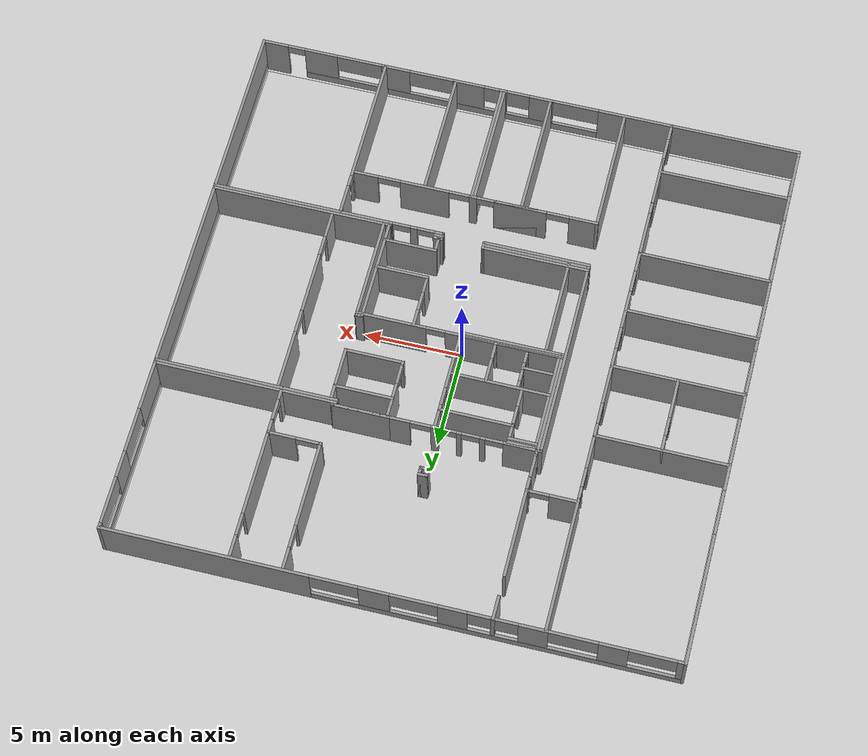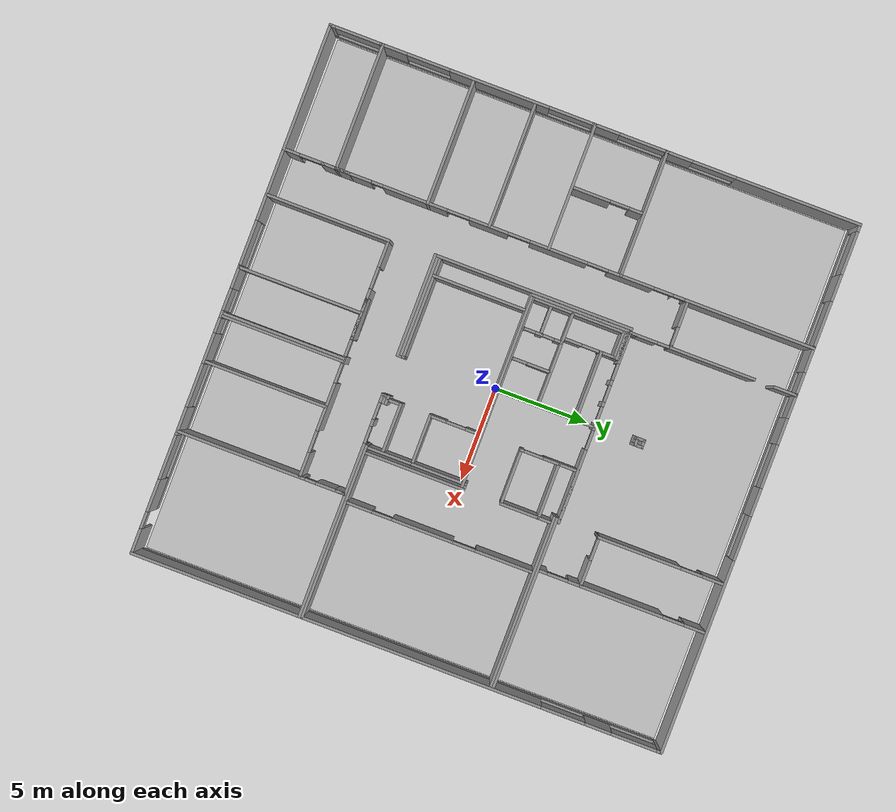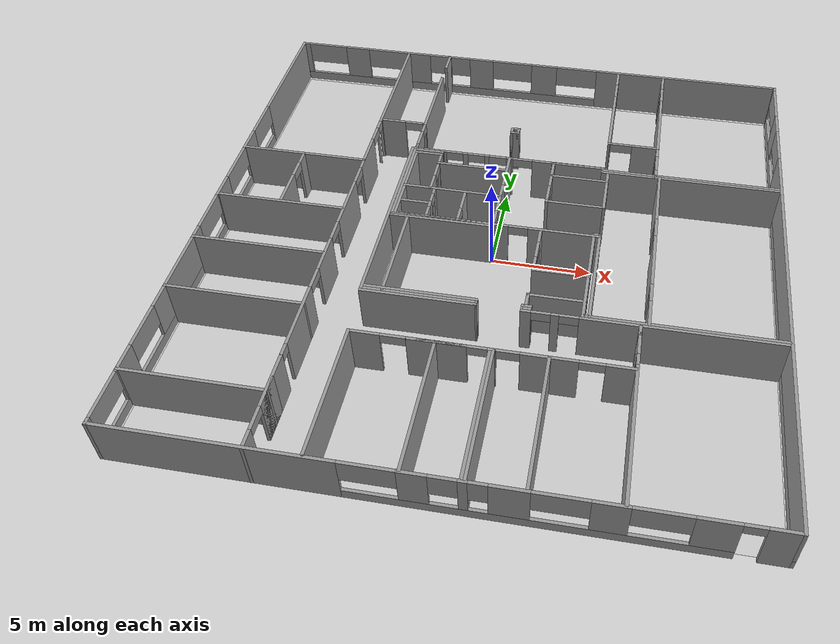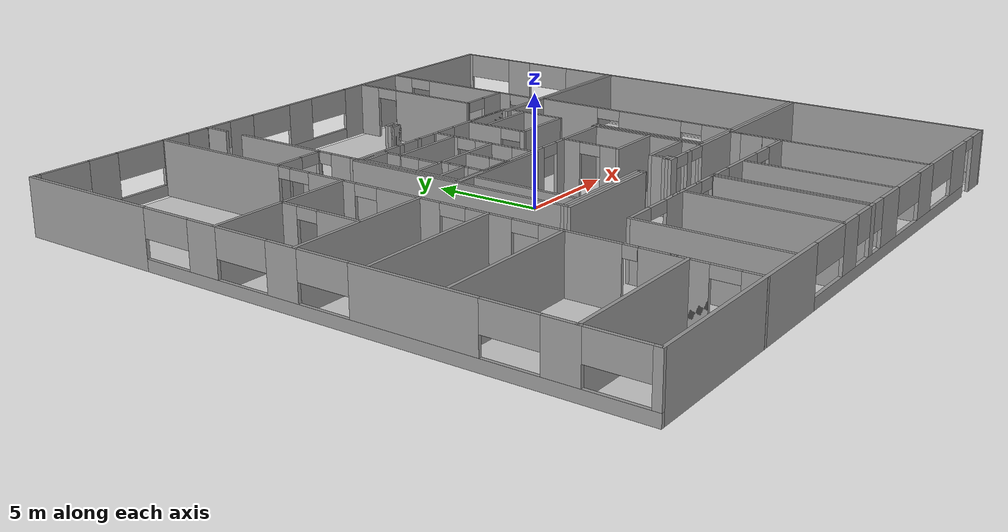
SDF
<sdf version="1.6">
 <world name="default">
  <plugin name="gazebo_ros_state" filename="libgazebo_ros_state.so">
   <ros><namespace>/gazebo</namespace></ros>
   <update_rate>1.0</update_rate>
  </plugin>
  <light name="sun" type="directional">
   <pose>0 0 10 0 -0 0</pose>
   <diffuse>0.8 0.8 0.8 1</diffuse>
   <specular>0.1 0.1 0.1 1</specular>
   <attenuation>
    <range>1000</range>
    <constant>0.9</constant>
    <linear>0.01</linear>
    <quadratic>0.001</quadratic>
   </attenuation>
   <direction>-0.5 0.5 -1</direction>
  </light>
  <model name="my_ground_plane">
   <static>1</static>
   <link name="link">
    <collision name="collision">
     <geometry><plane><normal>0 0 1</normal><size>100 100</size></plane></geometry>
     <surface><friction><ode><mu>100</mu><mu2>50</mu2></ode></friction></surface>
    </collision>
    <visual name="visual">
     <cast_shadows>0</cast_shadows>
     <geometry><plane><normal>0 0 1</normal><size>28 28</size></plane></geometry>
     <material>
      <script>
       <uri>model://my_ground_plane/materials/scripts</uri>
       <uri>model://my_ground_plane/materials/textures</uri>
       <name>MyGroundPlane/Image</name>
      </script>
     </material>
    </visual>
   </link>
  </model>
  <gravity>0 0 -9.8</gravity>
  <magnetic_field>6e-06 2.3e-05 -4.2e-05</magnetic_field>
  <atmosphere type="adiabatic"/>
  <physics name="default_physics" default="0" type="ode">
   <max_step_size>0.001</max_step_size>
   <real_time_factor>1</real_time_factor>
   <real_time_update_rate>1000</real_time_update_rate>
  </physics>
  <scene>
   <ambient>0.4 0.4 0.4 1</ambient>
   <background>0.7 0.7 0.7 1</background>
   <shadows>1</shadows>
   <sky><clouds><speed>12</speed></clouds></sky>
  </scene>
  <spherical_coordinates>
   <surface_model>EARTH_WGS84</surface_model>
   <latitude_deg>0</latitude_deg>
   <longitude_deg>0</longitude_deg>
   <elevation>0</elevation>
   <heading_deg>0</heading_deg>
  </spherical_coordinates>
  <model name="basement">
   <link name="Wall_1">
    <pose>-14.1254 0.001772 0 0 0 -1.5708</pose>
    <visual name="Wall_1_Visual_0">
     <pose>-10.8889 0 1.25 0 -0 0</pose>
     <geometry><box><size>6.72223 0.15 2.5</size></box></geometry>
     <material>
      <script><uri>file://media/materials/scripts/gazebo.material</uri><name>Gazebo/Grey</name></script>
      <ambient>1 1 1 1</ambient>
     </material>
    </visual>
    <collision name="Wall_1_Collision_0">
     <geometry><box><size>6.72223 0.15 2.5</size></box></geometry>
     <pose>-10.8889 0 1.25 0 -0 0</pose>
    </collision>
    <visual name="Wall_1_Visual_1">
     <pose>3.36112 0 0.25 0 -0 0</pose>
     <geometry><box><size>21.7778 0.15 0.5</size></box></geometry>
     <material>
      <script><uri>file://media/materials/scripts/gazebo.material</uri><name>Gazebo/Grey</name></script>
      <ambient>1 1 1 1</ambient>
     </material>
    </visual>
    <collision name="Wall_1_Collision_1">
     <geometry><box><size>21.7778 0.15 0.5</size></box></geometry>
     <pose>3.36112 0 0.25 0 -0 0</pose>
    </collision>
    <visual name="Wall_1_Visual_2">
     <pose>-4.48488 0 1.5 0 -0 0</pose>
     <geometry><box><size>1.45334 0.15 2</size></box></geometry>
     <material>
      <script><uri>file://media/materials/scripts/gazebo.material</uri><name>Gazebo/Grey</name></script>
      <ambient>1 1 1 1</ambient>
     </material>
    </visual>
    <collision name="Wall_1_Collision_2">
     <geometry><box><size>1.45334 0.15 2</size></box></geometry>
     <pose>-4.48488 0 1.5 0 -0 0</pose>
    </collision>
    <visual name="Wall_1_Visual_3">
     <pose>-0.57841 0 1.5 0 -0 0</pose>
     <geometry><box><size>1.45641 0.15 2</size></box></geometry>
     <material>
      <script><uri>file://media/materials/scripts/gazebo.material</uri><name>Gazebo/Grey</name></script>
      <ambient>1 1 1 1</ambient>
     </material>
    </visual>
    <collision name="Wall_1_Collision_3">
     <geometry><box><size>1.45641 0.15 2</size></box></geometry>
     <pose>-0.57841 0 1.5 0 -0 0</pose>
    </collision>
    <visual name="Wall_1_Visual_4">
     <pose>5.12077 0 1.5 0 -0 0</pose>
     <geometry><box><size>5.31789 0.15 2</size></box></geometry>
     <material>
      <script><uri>file://media/materials/scripts/gazebo.material</uri><name>Gazebo/Grey</name></script>
      <ambient>1 1 1 1</ambient>
     </material>
    </visual>
    <collision name="Wall_1_Collision_4">
     <geometry><box><size>5.31789 0.15 2</size></box></geometry>
     <pose>5.12077 0 1.5 0 -0 0</pose>
    </collision>
    <visual name="Wall_1_Visual_5">
     <pose>10.7967 0 1.5 0 -0 0</pose>
     <geometry><box><size>1.45641 0.15 2</size></box></geometry>
     <material>
      <script><uri>file://media/materials/scripts/gazebo.material</uri><name>Gazebo/Grey</name></script>
      <ambient>1 1 1 1</ambient>
     </material>
    </visual>
    <collision name="Wall_1_Collision_5">
     <geometry><box><size>1.45641 0.15 2</size></box></geometry>
     <pose>10.7967 0 1.5 0 -0 0</pose>
    </collision>
    <visual name="Wall_1_Visual_6">
     <pose>14.0784 0 1.5 0 -0 0</pose>
     <geometry><box><size>0.343295 0.15 2</size></box></geometry>
     <material>
      <script><uri>file://media/materials/scripts/gazebo.material</uri><name>Gazebo/Grey</name></script>
      <ambient>1 1 1 1</ambient>
     </material>
    </visual>
    <collision name="Wall_1_Collision_6">
     <geometry><box><size>0.343295 0.15 2</size></box></geometry>
     <pose>14.0784 0 1.5 0 -0 0</pose>
    </collision>
    <visual name="Wall_1_Visual_7">
     <pose>-6.36966 0 1.9 0 -0 0</pose>
     <geometry><box><size>2.31621 0.15 1.2</size></box></geometry>
     <material>
      <script><uri>file://media/materials/scripts/gazebo.material</uri><name>Gazebo/Grey</name></script>
      <ambient>1 1 1 1</ambient>
     </material>
    </visual>
    <collision name="Wall_1_Collision_7">
     <geometry><box><size>2.31621 0.15 1.2</size></box></geometry>
     <pose>-6.36966 0 1.9 0 -0 0</pose>
    </collision>
    <visual name="Wall_1_Visual_8">
     <pose>-2.53241 0 1.9 0 -0 0</pose>
     <geometry><box><size>2.4516 0.15 1.2</size></box></geometry>
     <material>
      <script><uri>file://media/materials/scripts/gazebo.material</uri><name>Gazebo/Grey</name></script>
      <ambient>1 1 1 1</ambient>
     </material>
    </visual>
    <collision name="Wall_1_Collision_8">
     <geometry><box><size>2.4516 0.15 1.2</size></box></geometry>
     <pose>-2.53241 0 1.9 0 -0 0</pose>
    </collision>
    <visual name="Wall_1_Visual_9">
     <pose>1.30581 0 1.9 0 -0 0</pose>
     <geometry><box><size>2.31203 0.15 1.2</size></box></geometry>
     <material>
      <script><uri>file://media/materials/scripts/gazebo.material</uri><name>Gazebo/Grey</name></script>
      <ambient>1 1 1 1</ambient>
     </material>
    </visual>
    <collision name="Wall_1_Collision_9">
     <geometry><box><size>2.31203 0.15 1.2</size></box></geometry>
     <pose>1.30581 0 1.9 0 -0 0</pose>
    </collision>
    <visual name="Wall_1_Visual_10">
     <pose>8.9241 0 1.9 0 -0 0</pose>
     <geometry><box><size>2.28877 0.15 1.2</size></box></geometry>
     <material>
      <script><uri>file://media/materials/scripts/gazebo.material</uri><name>Gazebo/Grey</name></script>
      <ambient>1 1 1 1</ambient>
     </material>
    </visual>
    <collision name="Wall_1_Collision_10">
     <geometry><box><size>2.28877 0.15 1.2</size></box></geometry>
     <pose>8.9241 0 1.9 0 -0 0</pose>
    </collision>
    <visual name="Wall_1_Visual_11">
     <pose>12.7158 0 1.9 0 -0 0</pose>
     <geometry><box><size>2.38181 0.15 1.2</size></box></geometry>
     <material>
      <script><uri>file://media/materials/scripts/gazebo.material</uri><name>Gazebo/Grey</name></script>
      <ambient>1 1 1 1</ambient>
     </material>
    </visual>
    <collision name="Wall_1_Collision_11">
     <geometry><box><size>2.38181 0.15 1.2</size></box></geometry>
     <pose>12.7158 0 1.9 0 -0 0</pose>
    </collision>
   </link>
   <link name="Wall_100">
    <pose>8.19919 -5.19776 0 0 -0 0</pose>
    <visual name="Wall_100_Visual_0">
     <pose>-5.7562 0 1.25 0 -0 0</pose>
     <geometry><box><size>0.487607 0.15 2.5</size></box></geometry>
     <material>
      <script><uri>file://media/materials/scripts/gazebo.material</uri><name>Gazebo/Grey</name></script>
      <ambient>1 1 1 1</ambient>
     </material>
    </visual>
    <collision name="Wall_100_Collision_0">
     <geometry><box><size>0.487607 0.15 2.5</size></box></geometry>
     <pose>-5.7562 0 1.25 0 -0 0</pose>
    </collision>
    <visual name="Wall_100_Visual_1">
     <pose>-4.42761 0 1.25 0 -0 0</pose>
     <geometry><box><size>0.369565 0.15 2.5</size></box></geometry>
     <material>
      <script><uri>file://media/materials/scripts/gazebo.material</uri><name>Gazebo/Grey</name></script>
      <ambient>1 1 1 1</ambient>
     </material>
    </visual>
    <collision name="Wall_100_Collision_1">
     <geometry><box><size>0.369565 0.15 2.5</size></box></geometry>
     <pose>-4.42761 0 1.25 0 -0 0</pose>
    </collision>
    <visual name="Wall_100_Visual_2">
     <pose>1.32859 0 1.25 0 -0 0</pose>
     <geometry><box><size>9.34283 0.15 2.5</size></box></geometry>
     <material>
      <script><uri>file://media/materials/scripts/gazebo.material</uri><name>Gazebo/Grey</name></script>
      <ambient>1 1 1 1</ambient>
     </material>
    </visual>
    <collision name="Wall_100_Collision_2">
     <geometry><box><size>9.34283 0.15 2.5</size></box></geometry>
     <pose>1.32859 0 1.25 0 -0 0</pose>
    </collision>
    <visual name="Wall_100_Visual_3">
     <pose>-5.06239 0 2.25 0 -0 0</pose>
     <geometry><box><size>0.9 0.15 0.5</size></box></geometry>
     <material>
      <script><uri>file://media/materials/scripts/gazebo.material</uri><name>Gazebo/Grey</name></script>
      <ambient>1 1 1 1</ambient>
     </material>
    </visual>
    <collision name="Wall_100_Collision_3">
     <geometry><box><size>0.9 0.15 0.5</size></box></geometry>
     <pose>-5.06239 0 2.25 0 -0 0</pose>
    </collision>
    <visual name="Wall_100_Visual_4">
     <pose>-3.79283 0 2.25 0 -0 0</pose>
     <geometry><box><size>0.9 0.15 0.5</size></box></geometry>
     <material>
      <script><uri>file://media/materials/scripts/gazebo.material</uri><name>Gazebo/Grey</name></script>
      <ambient>1 1 1 1</ambient>
     </material>
    </visual>
    <collision name="Wall_100_Collision_4">
     <geometry><box><size>0.9 0.15 0.5</size></box></geometry>
     <pose>-3.79283 0 2.25 0 -0 0</pose>
    </collision>
   </link>
   <link name="Wall_102">
    <collision name="Wall_102_Collision">
     <geometry><box><size>9.25 0.15 2.5</size></box></geometry>
     <pose>0 0 1.25 0 -0 0</pose>
    </collision>
    <visual name="Wall_102_Visual">
     <pose>0 0 1.25 0 -0 0</pose>
     <geometry><box><size>9.25 0.15 2.5</size></box></geometry>
     <material>
      <script><uri>file://media/materials/scripts/gazebo.material</uri><name>Gazebo/Grey</name></script>
      <ambient>1 1 1 1</ambient>
     </material>
    </visual>
    <pose>9.51475 -5.05392 0 0 -0 0</pose>
   </link>
   <link name="Wall_104">
    <collision name="Wall_104_Collision">
     <geometry><box><size>5.5 0.15 2.5</size></box></geometry>
     <pose>0 0 1.25 0 -0 0</pose>
    </collision>
    <visual name="Wall_104_Visual">
     <pose>0 0 1.25 0 -0 0</pose>
     <geometry><box><size>5.5 0.15 2.5</size></box></geometry>
     <material>
      <script><uri>file://media/materials/scripts/gazebo.material</uri><name>Gazebo/Grey</name></script>
      <ambient>1 1 1 1</ambient>
     </material>
    </visual>
    <pose>5.28935 -2.40756 0 0 0 -1.5708</pose>
   </link>
   <link name="Wall_108">
    <pose>2.7255 0.139626 0 0 -0 0</pose>
    <visual name="Wall_108_Visual_0">
     <pose>-2.26972 0 1.25 0 -0 0</pose>
     <geometry><box><size>0.710554 0.15 2.5</size></box></geometry>
     <material>
      <script><uri>file://media/materials/scripts/gazebo.material</uri><name>Gazebo/Grey</name></script>
      <ambient>1 1 1 1</ambient>
     </material>
    </visual>
    <collision name="Wall_108_Collision_0">
     <geometry><box><size>0.710554 0.15 2.5</size></box></geometry>
     <pose>-2.26972 0 1.25 0 -0 0</pose>
    </collision>
    <visual name="Wall_108_Visual_1">
     <pose>0.840079 0 1.25 0 -0 0</pose>
     <geometry><box><size>3.56984 0.15 2.5</size></box></geometry>
     <material>
      <script><uri>file://media/materials/scripts/gazebo.material</uri><name>Gazebo/Grey</name></script>
      <ambient>1 1 1 1</ambient>
     </material>
    </visual>
    <collision name="Wall_108_Collision_1">
     <geometry><box><size>3.56984 0.15 2.5</size></box></geometry>
     <pose>0.840079 0 1.25 0 -0 0</pose>
    </collision>
    <visual name="Wall_108_Visual_2">
     <pose>-1.42964 0 2.25 0 -0 0</pose>
     <geometry><box><size>0.969605 0.15 0.5</size></box></geometry>
     <material>
      <script><uri>file://media/materials/scripts/gazebo.material</uri><name>Gazebo/Grey</name></script>
      <ambient>1 1 1 1</ambient>
     </material>
    </visual>
    <collision name="Wall_108_Collision_2">
     <geometry><box><size>0.969605 0.15 0.5</size></box></geometry>
     <pose>-1.42964 0 2.25 0 -0 0</pose>
    </collision>
   </link>
   <link name="Wall_11">
    <collision name="Wall_11_Collision">
     <geometry><box><size>6.75 0.15 2.5</size></box></geometry>
     <pose>0 0 1.25 0 -0 0</pose>
    </collision>
    <visual name="Wall_11_Visual">
     <pose>0 0 1.25 0 -0 0</pose>
     <geometry><box><size>6.75 0.15 2.5</size></box></geometry>
     <material>
      <script><uri>file://media/materials/scripts/gazebo.material</uri><name>Gazebo/Grey</name></script>
      <ambient>1 1 1 1</ambient>
     </material>
    </visual>
    <pose>-10.8091 -11.3705 0 0 -0 0</pose>
   </link>
   <link name="Wall_112">
    <collision name="Wall_112_Collision">
     <geometry><box><size>5.5 0.15 2.5</size></box></geometry>
     <pose>0 0 1.25 0 -0 0</pose>
    </collision>
    <visual name="Wall_112_Visual">
     <pose>0 0 1.25 0 -0 0</pose>
     <geometry><box><size>5.5 0.15 2.5</size></box></geometry>
     <material>
      <script><uri>file://media/materials/scripts/gazebo.material</uri><name>Gazebo/Grey</name></script>
      <ambient>1 1 1 1</ambient>
     </material>
    </visual>
    <pose>5.00796 -2.4103 0 0 0 -1.5708</pose>
   </link>
   <link name="Wall_116">
    <collision name="Wall_116_Collision">
     <geometry><box><size>0.4 0.15 2.5</size></box></geometry>
     <pose>0 0 1.25 0 -0 0</pose>
    </collision>
    <visual name="Wall_116_Visual">
     <pose>0 0 1.25 0 -0 0</pose>
     <geometry><box><size>0.4 0.15 2.5</size></box></geometry>
     <material>
      <script><uri>file://media/materials/scripts/gazebo.material</uri><name>Gazebo/Grey</name></script>
      <ambient>1 1 1 1</ambient>
     </material>
    </visual>
    <pose>5.13257 0.268093 0 0 -0 0</pose>
   </link>
   <link name="Wall_118">
    <pose>2.41948 -1.1745 0 0 -0 1.5708</pose>
    <visual name="Wall_118_Visual_0">
     <pose>-0.97086 0 1.25 0 -0 0</pose>
     <geometry><box><size>0.808281 0.15 2.5</size></box></geometry>
     <material>
      <script><uri>file://media/materials/scripts/gazebo.material</uri><name>Gazebo/Grey</name></script>
      <ambient>1 1 1 1</ambient>
     </material>
    </visual>
    <collision name="Wall_118_Collision_0">
     <geometry><box><size>0.808281 0.15 2.5</size></box></geometry>
     <pose>-0.97086 0 1.25 0 -0 0</pose>
    </collision>
    <visual name="Wall_118_Visual_1">
     <pose>0.913802 0 1.25 0 -0 0</pose>
     <geometry><box><size>0.922397 0.15 2.5</size></box></geometry>
     <material>
      <script><uri>file://media/materials/scripts/gazebo.material</uri><name>Gazebo/Grey</name></script>
      <ambient>1 1 1 1</ambient>
     </material>
    </visual>
    <collision name="Wall_118_Collision_1">
     <geometry><box><size>0.922397 0.15 2.5</size></box></geometry>
     <pose>0.913802 0 1.25 0 -0 0</pose>
    </collision>
    <visual name="Wall_118_Visual_2">
     <pose>-0.057058 0 2.25 0 -0 0</pose>
     <geometry><box><size>1.01932 0.15 0.5</size></box></geometry>
     <material>
      <script><uri>file://media/materials/scripts/gazebo.material</uri><name>Gazebo/Grey</name></script>
      <ambient>1 1 1 1</ambient>
     </material>
    </visual>
    <collision name="Wall_118_Collision_2">
     <geometry><box><size>1.01932 0.15 0.5</size></box></geometry>
     <pose>-0.057058 0 2.25 0 -0 0</pose>
    </collision>
   </link>
   <link name="Wall_120">
    <collision name="Wall_120_Collision">
     <geometry><box><size>2.75 0.15 2.5</size></box></geometry>
     <pose>0 0 1.25 0 -0 0</pose>
    </collision>
    <visual name="Wall_120_Visual">
     <pose>0 0 1.25 0 -0 0</pose>
     <geometry><box><size>2.75 0.15 2.5</size></box></geometry>
     <material>
      <script><uri>file://media/materials/scripts/gazebo.material</uri><name>Gazebo/Grey</name></script>
      <ambient>1 1 1 1</ambient>
     </material>
    </visual>
    <pose>3.71948 -2.60376 0 0 -0 0</pose>
   </link>
   <link name="Wall_122">
    <collision name="Wall_122_Collision">
     <geometry><box><size>2.75 0.15 2.5</size></box></geometry>
     <pose>0 0 1.25 0 -0 0</pose>
    </collision>
    <visual name="Wall_122_Visual">
     <pose>0 0 1.25 0 -0 0</pose>
     <geometry><box><size>2.75 0.15 2.5</size></box></geometry>
     <material>
      <script><uri>file://media/materials/scripts/gazebo.material</uri><name>Gazebo/Grey</name></script>
      <ambient>1 1 1 1</ambient>
     </material>
    </visual>
    <pose>3.71502 -4.18637 0 0 -0 0</pose>
   </link>
   <link name="Wall_124">
    <collision name="Wall_124_Collision">
     <geometry><box><size>0.5 0.15 2.5</size></box></geometry>
     <pose>0 0 1.25 0 -0 0</pose>
    </collision>
    <visual name="Wall_124_Visual">
     <pose>0 0 1.25 0 -0 0</pose>
     <geometry><box><size>0.5 0.15 2.5</size></box></geometry>
     <material>
      <script><uri>file://media/materials/scripts/gazebo.material</uri><name>Gazebo/Grey</name></script>
      <ambient>1 1 1 1</ambient>
     </material>
    </visual>
    <pose>2.45081 -4.90231 0 0 -0 0</pose>
   </link>
   <link name="Wall_126">
    <collision name="Wall_126_Collision">
     <geometry><box><size>0.4 0.15 2.5</size></box></geometry>
     <pose>0 0 1.25 0 -0 0</pose>
    </collision>
    <visual name="Wall_126_Visual">
     <pose>0 0 1.25 0 -0 0</pose>
     <geometry><box><size>0.4 0.15 2.5</size></box></geometry>
     <material>
      <script><uri>file://media/materials/scripts/gazebo.material</uri><name>Gazebo/Grey</name></script>
      <ambient>1 1 1 1</ambient>
     </material>
    </visual>
    <pose>2.27581 -5.05714 0 0 0 -1.5708</pose>
   </link>
   <link name="Wall_128">
    <collision name="Wall_128_Collision">
     <geometry><box><size>0.75 0.15 2.5</size></box></geometry>
     <pose>0 0 1.25 0 -0 0</pose>
    </collision>
    <visual name="Wall_128_Visual">
     <pose>0 0 1.25 0 -0 0</pose>
     <geometry><box><size>0.75 0.15 2.5</size></box></geometry>
     <material>
      <script><uri>file://media/materials/scripts/gazebo.material</uri><name>Gazebo/Grey</name></script>
      <ambient>1 1 1 1</ambient>
     </material>
    </visual>
    <pose>2.41502 -4.54603 0 0 0 -1.5708</pose>
   </link>
   <link name="Wall_13">
    <collision name="Wall_13_Collision">
     <geometry><box><size>6.75 0.15 2.5</size></box></geometry>
     <pose>0 0 1.25 0 -0 0</pose>
    </collision>
    <visual name="Wall_13_Visual">
     <pose>0 0 1.25 0 -0 0</pose>
     <geometry><box><size>6.75 0.15 2.5</size></box></geometry>
     <material>
      <script><uri>file://media/materials/scripts/gazebo.material</uri><name>Gazebo/Grey</name></script>
      <ambient>1 1 1 1</ambient>
     </material>
    </visual>
    <pose>-10.8096 -6.47351 0 0 -0 0</pose>
   </link>
   <link name="Wall_130">
    <pose>7.59342 -9.67316 0 0 -0 1.5708</pose>
    <visual name="Wall_130_Visual_0">
     <pose>-1.10011 0 1.25 0 -0 0</pose>
     <geometry><box><size>6.79978 0.15 2.5</size></box></geometry>
     <material>
      <script><uri>file://media/materials/scripts/gazebo.material</uri><name>Gazebo/Grey</name></script>
      <ambient>1 1 1 1</ambient>
     </material>
    </visual>
    <collision name="Wall_130_Collision_0">
     <geometry><box><size>6.79978 0.15 2.5</size></box></geometry>
     <pose>-1.10011 0 1.25 0 -0 0</pose>
    </collision>
    <visual name="Wall_130_Visual_1">
     <pose>3.69951 0 1.25 0 -0 0</pose>
     <geometry><box><size>1.60098 0.15 2.5</size></box></geometry>
     <material>
      <script><uri>file://media/materials/scripts/gazebo.material</uri><name>Gazebo/Grey</name></script>
      <ambient>1 1 1 1</ambient>
     </material>
    </visual>
    <collision name="Wall_130_Collision_1">
     <geometry><box><size>1.60098 0.15 2.5</size></box></geometry>
     <pose>3.69951 0 1.25 0 -0 0</pose>
    </collision>
    <visual name="Wall_130_Visual_2">
     <pose>4.21195 0 1.25 0 -0 0</pose>
     <geometry><box><size>0.576095 0.15 2.5</size></box></geometry>
     <material>
      <script><uri>file://media/materials/scripts/gazebo.material</uri><name>Gazebo/Grey</name></script>
      <ambient>1 1 1 1</ambient>
     </material>
    </visual>
    <collision name="Wall_130_Collision_2">
     <geometry><box><size>0.576095 0.15 2.5</size></box></geometry>
     <pose>4.21195 0 1.25 0 -0 0</pose>
    </collision>
    <visual name="Wall_130_Visual_3">
     <pose>2.59646 0 2.25 0 -0 0</pose>
     <geometry><box><size>0.593362 0.15 0.5</size></box></geometry>
     <material>
      <script><uri>file://media/materials/scripts/gazebo.material</uri><name>Gazebo/Grey</name></script>
      <ambient>1 1 1 1</ambient>
     </material>
    </visual>
    <collision name="Wall_130_Collision_3">
     <geometry><box><size>0.593362 0.15 0.5</size></box></geometry>
     <pose>2.59646 0 2.25 0 -0 0</pose>
    </collision>
   </link>
   <link name="Wall_132">
    <collision name="Wall_132_Collision">
     <geometry><box><size>6.6 0.15 2.5</size></box></geometry>
     <pose>0 0 1.25 0 -0 0</pose>
    </collision>
    <visual name="Wall_132_Visual">
     <pose>0 0 1.25 0 -0 0</pose>
     <geometry><box><size>6.6 0.15 2.5</size></box></geometry>
     <material>
      <script><uri>file://media/materials/scripts/gazebo.material</uri><name>Gazebo/Grey</name></script>
      <ambient>1 1 1 1</ambient>
     </material>
    </visual>
    <pose>-5.06165 -10.8664 0 0 0 -1.5708</pose>
   </link>
   <link name="Wall_134">
    <pose>1.23835 -7.64141 0 0 -0 0</pose>
    <visual name="Wall_134_Visual_0">
     <pose>-5.62659 0 1.25 0 -0 0</pose>
     <geometry><box><size>1.49682 0.15 2.5</size></box></geometry>
     <material>
      <script><uri>file://media/materials/scripts/gazebo.material</uri><name>Gazebo/Grey</name></script>
      <ambient>1 1 1 1</ambient>
     </material>
    </visual>
    <collision name="Wall_134_Collision_0">
     <geometry><box><size>1.49682 0.15 2.5</size></box></geometry>
     <pose>-5.62659 0 1.25 0 -0 0</pose>
    </collision>
    <visual name="Wall_134_Visual_1">
     <pose>-2.35576 0 1.25 0 -0 0</pose>
     <geometry><box><size>2.70875 0.15 2.5</size></box></geometry>
     <material>
      <script><uri>file://media/materials/scripts/gazebo.material</uri><name>Gazebo/Grey</name></script>
      <ambient>1 1 1 1</ambient>
     </material>
    </visual>
    <collision name="Wall_134_Collision_1">
     <geometry><box><size>2.70875 0.15 2.5</size></box></geometry>
     <pose>-2.35576 0 1.25 0 -0 0</pose>
    </collision>
    <visual name="Wall_134_Visual_2">
     <pose>-2.12152 0 1.25 0 -0 0</pose>
     <geometry><box><size>2.24027 0.15 2.5</size></box></geometry>
     <material>
      <script><uri>file://media/materials/scripts/gazebo.material</uri><name>Gazebo/Grey</name></script>
      <ambient>1 1 1 1</ambient>
     </material>
    </visual>
    <collision name="Wall_134_Collision_2">
     <geometry><box><size>2.24027 0.15 2.5</size></box></geometry>
     <pose>-2.12152 0 1.25 0 -0 0</pose>
    </collision>
    <visual name="Wall_134_Visual_3">
     <pose>0.087487 0 1.25 0 -0 0</pose>
     <geometry><box><size>0.377744 0.15 2.5</size></box></geometry>
     <material>
      <script><uri>file://media/materials/scripts/gazebo.material</uri><name>Gazebo/Grey</name></script>
      <ambient>1 1 1 1</ambient>
     </material>
    </visual>
    <collision name="Wall_134_Collision_3">
     <geometry><box><size>0.377744 0.15 2.5</size></box></geometry>
     <pose>0.087487 0 1.25 0 -0 0</pose>
    </collision>
    <visual name="Wall_134_Visual_4">
     <pose>2.60072 0 1.25 0 -0 0</pose>
     <geometry><box><size>2.55041 0.15 2.5</size></box></geometry>
     <material>
      <script><uri>file://media/materials/scripts/gazebo.material</uri><name>Gazebo/Grey</name></script>
      <ambient>1 1 1 1</ambient>
     </material>
    </visual>
    <collision name="Wall_134_Collision_4">
     <geometry><box><size>2.55041 0.15 2.5</size></box></geometry>
     <pose>2.60072 0 1.25 0 -0 0</pose>
    </collision>
    <visual name="Wall_134_Visual_5">
     <pose>5.69975 0 1.25 0 -0 0</pose>
     <geometry><box><size>1.35049 0.15 2.5</size></box></geometry>
     <material>
      <script><uri>file://media/materials/scripts/gazebo.material</uri><name>Gazebo/Grey</name></script>
      <ambient>1 1 1 1</ambient>
     </material>
    </visual>
    <collision name="Wall_134_Collision_5">
     <geometry><box><size>1.35049 0.15 2.5</size></box></geometry>
     <pose>5.69975 0 1.25 0 -0 0</pose>
    </collision>
    <visual name="Wall_134_Visual_6">
     <pose>-4.29684 0 2.25 0 -0 0</pose>
     <geometry><box><size>1.16267 0.15 0.5</size></box></geometry>
     <material>
      <script><uri>file://media/materials/scripts/gazebo.material</uri><name>Gazebo/Grey</name></script>
      <ambient>1 1 1 1</ambient>
     </material>
    </visual>
    <collision name="Wall_134_Collision_6">
     <geometry><box><size>1.16267 0.15 0.5</size></box></geometry>
     <pose>-4.29684 0 2.25 0 -0 0</pose>
    </collision>
    <visual name="Wall_134_Visual_7">
     <pose>-0.551385 0 2.25 0 -0 0</pose>
     <geometry><box><size>0.9 0.15 0.5</size></box></geometry>
     <material>
      <script><uri>file://media/materials/scripts/gazebo.material</uri><name>Gazebo/Grey</name></script>
      <ambient>1 1 1 1</ambient>
     </material>
    </visual>
    <collision name="Wall_134_Collision_7">
     <geometry><box><size>0.9 0.15 0.5</size></box></geometry>
     <pose>-0.551385 0 2.25 0 -0 0</pose>
    </collision>
    <visual name="Wall_134_Visual_8">
     <pose>-0.551385 0 2.25 0 -0 0</pose>
     <geometry><box><size>0.9 0.15 0.5</size></box></geometry>
     <material>
      <script><uri>file://media/materials/scripts/gazebo.material</uri><name>Gazebo/Grey</name></script>
      <ambient>1 1 1 1</ambient>
     </material>
    </visual>
    <collision name="Wall_134_Collision_8">
     <geometry><box><size>0.9 0.15 0.5</size></box></geometry>
     <pose>-0.551385 0 2.25 0 -0 0</pose>
    </collision>
    <visual name="Wall_134_Visual_9">
     <pose>0.800936 0 2.25 0 -0 0</pose>
     <geometry><box><size>1.04915 0.15 0.5</size></box></geometry>
     <material>
      <script><uri>file://media/materials/scripts/gazebo.material</uri><name>Gazebo/Grey</name></script>
      <ambient>1 1 1 1</ambient>
     </material>
    </visual>
    <collision name="Wall_134_Collision_9">
     <geometry><box><size>1.04915 0.15 0.5</size></box></geometry>
     <pose>0.800936 0 2.25 0 -0 0</pose>
    </collision>
    <visual name="Wall_134_Visual_10">
     <pose>4.45021 0 2.25 0 -0 0</pose>
     <geometry><box><size>1.14859 0.15 0.5</size></box></geometry>
     <material>
      <script><uri>file://media/materials/scripts/gazebo.material</uri><name>Gazebo/Grey</name></script>
      <ambient>1 1 1 1</ambient>
     </material>
    </visual>
    <collision name="Wall_134_Collision_10">
     <geometry><box><size>1.14859 0.15 0.5</size></box></geometry>
     <pose>4.45021 0 2.25 0 -0 0</pose>
    </collision>
   </link>
   <link name="Wall_136">
    <collision name="Wall_136_Collision">
     <geometry><box><size>6.5 0.15 2.5</size></box></geometry>
     <pose>0 0 1.25 0 -0 0</pose>
    </collision>
    <visual name="Wall_136_Visual">
     <pose>0 0 1.25 0 -0 0</pose>
     <geometry><box><size>6.5 0.15 2.5</size></box></geometry>
     <material>
      <script><uri>file://media/materials/scripts/gazebo.material</uri><name>Gazebo/Grey</name></script>
      <ambient>1 1 1 1</ambient>
     </material>
    </visual>
    <pose>-1.17554 -10.926 0 0 -0 1.5708</pose>
   </link>
   <link name="Wall_138">
    <collision name="Wall_138_Collision">
     <geometry><box><size>6.5 0.15 2.5</size></box></geometry>
     <pose>0 0 1.25 0 -0 0</pose>
    </collision>
    <visual name="Wall_138_Visual">
     <pose>0 0 1.25 0 -0 0</pose>
     <geometry><box><size>6.5 0.15 2.5</size></box></geometry>
     <material>
      <script><uri>file://media/materials/scripts/gazebo.material</uri><name>Gazebo/Grey</name></script>
      <ambient>1 1 1 1</ambient>
     </material>
    </visual>
    <pose>1.2636 -10.87 0 0 -0 1.5708</pose>
   </link>
   <link name="Wall_140">
    <collision name="Wall_140_Collision">
     <geometry><box><size>6.5 0.15 2.5</size></box></geometry>
     <pose>0 0 1.25 0 -0 0</pose>
    </collision>
    <visual name="Wall_140_Visual">
     <pose>0 0 1.25 0 -0 0</pose>
     <geometry><box><size>6.5 0.15 2.5</size></box></geometry>
     <material>
      <script><uri>file://media/materials/scripts/gazebo.material</uri><name>Gazebo/Grey</name></script>
      <ambient>1 1 1 1</ambient>
     </material>
    </visual>
    <pose>1.40771 -10.8804 0 0 0 -1.5708</pose>
   </link>
   <link name="Wall_142">
    <collision name="Wall_142_Collision">
     <geometry><box><size>6.5 0.15 2.5</size></box></geometry>
     <pose>0 0 1.25 0 -0 0</pose>
    </collision>
    <visual name="Wall_142_Visual">
     <pose>0 0 1.25 0 -0 0</pose>
     <geometry><box><size>6.5 0.15 2.5</size></box></geometry>
     <material>
      <script><uri>file://media/materials/scripts/gazebo.material</uri><name>Gazebo/Grey</name></script>
      <ambient>1 1 1 1</ambient>
     </material>
    </visual>
    <pose>3.84111 -10.8753 0 0 0 -1.5708</pose>
   </link>
   <link name="Wall_144">
    <collision name="Wall_144_Collision">
     <geometry><box><size>5.25 0.15 2.5</size></box></geometry>
     <pose>0 0 1.25 0 -0 0</pose>
    </collision>
    <visual name="Wall_144_Visual">
     <pose>0 0 1.25 0 -0 0</pose>
     <geometry><box><size>5.25 0.15 2.5</size></box></geometry>
     <material>
      <script><uri>file://media/materials/scripts/gazebo.material</uri><name>Gazebo/Grey</name></script>
      <ambient>1 1 1 1</ambient>
     </material>
    </visual>
    <pose>-2.51608 -5.05083 0 0 -0 0</pose>
   </link>
   <link name="Wall_146">
    <collision name="Wall_146_Collision">
     <geometry><box><size>5.25 0.15 2.5</size></box></geometry>
     <pose>0 0 1.25 0 -0 0</pose>
    </collision>
    <visual name="Wall_146_Visual">
     <pose>0 0 1.25 0 -0 0</pose>
     <geometry><box><size>5.25 0.15 2.5</size></box></geometry>
     <material>
      <script><uri>file://media/materials/scripts/gazebo.material</uri><name>Gazebo/Grey</name></script>
      <ambient>1 1 1 1</ambient>
     </material>
    </visual>
    <pose>-5.04892 2.61682 0 0 -0 1.5708</pose>
   </link>
   <link name="Wall_148">
    <collision name="Wall_148_Collision">
     <geometry><box><size>1.5 0.15 2.5</size></box></geometry>
     <pose>0 0 1.25 0 -0 0</pose>
    </collision>
    <visual name="Wall_148_Visual">
     <pose>0 0 1.25 0 -0 0</pose>
     <geometry><box><size>1.5 0.15 2.5</size></box></geometry>
     <material>
      <script><uri>file://media/materials/scripts/gazebo.material</uri><name>Gazebo/Grey</name></script>
      <ambient>1 1 1 1</ambient>
     </material>
    </visual>
    <pose>-4.23612 5.13065 0 0 -0 0</pose>
   </link>
   <link name="Wall_15">
    <collision name="Wall_15_Collision">
     <geometry><box><size>6.75 0.15 2.5</size></box></geometry>
     <pose>0 0 1.25 0 -0 0</pose>
    </collision>
    <visual name="Wall_15_Visual">
     <pose>0 0 1.25 0 -0 0</pose>
     <geometry><box><size>6.75 0.15 2.5</size></box></geometry>
     <material>
      <script><uri>file://media/materials/scripts/gazebo.material</uri><name>Gazebo/Grey</name></script>
      <ambient>1 1 1 1</ambient>
     </material>
    </visual>
    <pose>-10.8156 -3.17919 0 0 -0 0</pose>
   </link>
   <link name="Wall_150">
    <collision name="Wall_150_Collision">
     <geometry><box><size>1.5 0.15 2.5</size></box></geometry>
     <pose>0 0 1.25 0 -0 0</pose>
    </collision>
    <visual name="Wall_150_Visual">
     <pose>0 0 1.25 0 -0 0</pose>
     <geometry><box><size>1.5 0.15 2.5</size></box></geometry>
     <material>
      <script><uri>file://media/materials/scripts/gazebo.material</uri><name>Gazebo/Grey</name></script>
      <ambient>1 1 1 1</ambient>
     </material>
    </visual>
    <pose>-4.23669 5.20302 0 0 -0 0</pose>
   </link>
   <link name="Wall_152">
    <collision name="Wall_152_Collision">
     <geometry><box><size>5.25 0.15 2.5</size></box></geometry>
     <pose>0 0 1.25 0 -0 0</pose>
    </collision>
    <visual name="Wall_152_Visual">
     <pose>0 0 1.25 0 -0 0</pose>
     <geometry><box><size>5.25 0.15 2.5</size></box></geometry>
     <material>
      <script><uri>file://media/materials/scripts/gazebo.material</uri><name>Gazebo/Grey</name></script>
      <ambient>1 1 1 1</ambient>
     </material>
    </visual>
    <pose>-2.49774 0.066434 0 0 -0 0</pose>
   </link>
   <link name="Wall_154">
    <collision name="Wall_154_Collision">
     <geometry><box><size>0.4 0.15 2.5</size></box></geometry>
     <pose>0 0 1.25 0 -0 0</pose>
    </collision>
    <visual name="Wall_154_Visual">
     <pose>0 0 1.25 0 -0 0</pose>
     <geometry><box><size>0.4 0.15 2.5</size></box></geometry>
     <material>
      <script><uri>file://media/materials/scripts/gazebo.material</uri><name>Gazebo/Grey</name></script>
      <ambient>1 1 1 1</ambient>
     </material>
    </visual>
    <pose>2.49747 -5.04803 0 0 -0 0</pose>
   </link>
   <link name="Wall_17">
    <collision name="Wall_17_Collision">
     <geometry><box><size>6.75 0.15 2.5</size></box></geometry>
     <pose>0 0 1.25 0 -0 0</pose>
    </collision>
    <visual name="Wall_17_Visual">
     <pose>0 0 1.25 0 -0 0</pose>
     <geometry><box><size>6.75 0.15 2.5</size></box></geometry>
     <material>
      <script><uri>file://media/materials/scripts/gazebo.material</uri><name>Gazebo/Grey</name></script>
      <ambient>1 1 1 1</ambient>
     </material>
    </visual>
    <pose>-10.8156 0.004484 0 0 -0 0</pose>
   </link>
   <link name="Wall_19">
    <collision name="Wall_19_Collision">
     <geometry><box><size>6.75 0.15 2.5</size></box></geometry>
     <pose>0 0 1.25 0 -0 0</pose>
    </collision>
    <visual name="Wall_19_Visual">
     <pose>0 0 1.25 0 -0 0</pose>
     <geometry><box><size>6.75 0.15 2.5</size></box></geometry>
     <material>
      <script><uri>file://media/materials/scripts/gazebo.material</uri><name>Gazebo/Grey</name></script>
      <ambient>1 1 1 1</ambient>
     </material>
    </visual>
    <pose>-10.8156 3.85656 0 0 -0 0</pose>
   </link>
   <link name="Wall_2">
    <pose>-0.075421 -14.1732 0 0 -0 0</pose>
    <visual name="Wall_2_Visual_0">
     <pose>-8.86891 0 1.25 0 -0 0</pose>
     <geometry><box><size>10.5122 0.15 2.5</size></box></geometry>
     <material>
      <script><uri>file://media/materials/scripts/gazebo.material</uri><name>Gazebo/Grey</name></script>
      <ambient>1 1 1 1</ambient>
     </material>
    </visual>
    <collision name="Wall_2_Collision_0">
     <geometry><box><size>10.5122 0.15 2.5</size></box></geometry>
     <pose>-8.86891 0 1.25 0 -0 0</pose>
    </collision>
    <visual name="Wall_2_Visual_1">
     <pose>13.5044 0 1.25 0 -0 0</pose>
     <geometry><box><size>1.2411 0.15 2.5</size></box></geometry>
     <material>
      <script><uri>file://media/materials/scripts/gazebo.material</uri><name>Gazebo/Grey</name></script>
      <ambient>1 1 1 1</ambient>
     </material>
    </visual>
    <collision name="Wall_2_Collision_1">
     <geometry><box><size>1.2411 0.15 2.5</size></box></geometry>
     <pose>13.5044 0 1.25 0 -0 0</pose>
    </collision>
    <visual name="Wall_2_Visual_2">
     <pose>4.18554 0 0.25 0 -0 0</pose>
     <geometry><box><size>15.5967 0.15 0.5</size></box></geometry>
     <material>
      <script><uri>file://media/materials/scripts/gazebo.material</uri><name>Gazebo/Grey</name></script>
      <ambient>1 1 1 1</ambient>
     </material>
    </visual>
    <collision name="Wall_2_Collision_2">
     <geometry><box><size>15.5967 0.15 0.5</size></box></geometry>
     <pose>4.18554 0 0.25 0 -0 0</pose>
    </collision>
    <visual name="Wall_2_Visual_3">
     <pose>-0.601968 0 1.5 0 -0 0</pose>
     <geometry><box><size>1.2477 0.15 2</size></box></geometry>
     <material>
      <script><uri>file://media/materials/scripts/gazebo.material</uri><name>Gazebo/Grey</name></script>
      <ambient>1 1 1 1</ambient>
     </material>
    </visual>
    <collision name="Wall_2_Collision_3">
     <geometry><box><size>1.2477 0.15 2</size></box></geometry>
     <pose>-0.601968 0 1.5 0 -0 0</pose>
    </collision>
    <visual name="Wall_2_Visual_4">
     <pose>1.40722 0 1.5 0 -0 0</pose>
     <geometry><box><size>0.388736 0.15 2</size></box></geometry>
     <material>
      <script><uri>file://media/materials/scripts/gazebo.material</uri><name>Gazebo/Grey</name></script>
      <ambient>1 1 1 1</ambient>
     </material>
    </visual>
    <collision name="Wall_2_Collision_4">
     <geometry><box><size>0.388736 0.15 2</size></box></geometry>
     <pose>1.40722 0 1.5 0 -0 0</pose>
    </collision>
    <visual name="Wall_2_Visual_5">
     <pose>3.23091 0 1.5 0 -0 0</pose>
     <geometry><box><size>1.64359 0.15 2</size></box></geometry>
     <material>
      <script><uri>file://media/materials/scripts/gazebo.material</uri><name>Gazebo/Grey</name></script>
      <ambient>1 1 1 1</ambient>
     </material>
    </visual>
    <collision name="Wall_2_Collision_5">
     <geometry><box><size>1.64359 0.15 2</size></box></geometry>
     <pose>3.23091 0 1.5 0 -0 0</pose>
    </collision>
    <visual name="Wall_2_Visual_6">
     <pose>7.12509 0 1.5 0 -0 0</pose>
     <geometry><box><size>1.50721 0.15 2</size></box></geometry>
     <material>
      <script><uri>file://media/materials/scripts/gazebo.material</uri><name>Gazebo/Grey</name></script>
      <ambient>1 1 1 1</ambient>
     </material>
    </visual>
    <collision name="Wall_2_Collision_6">
     <geometry><box><size>1.50721 0.15 2</size></box></geometry>
     <pose>7.12509 0 1.5 0 -0 0</pose>
    </collision>
    <visual name="Wall_2_Visual_7">
     <pose>11.1159 0 1.5 0 -0 0</pose>
     <geometry><box><size>1.73607 0.15 2</size></box></geometry>
     <material>
      <script><uri>file://media/materials/scripts/gazebo.material</uri><name>Gazebo/Grey</name></script>
      <ambient>1 1 1 1</ambient>
     </material>
    </visual>
    <collision name="Wall_2_Collision_7">
     <geometry><box><size>1.73607 0.15 2</size></box></geometry>
     <pose>11.1159 0 1.5 0 -0 0</pose>
    </collision>
    <visual name="Wall_2_Visual_8">
     <pose>-2.41932 0 1.9 0 -0 0</pose>
     <geometry><box><size>2.387 0.15 1.2</size></box></geometry>
     <material>
      <script><uri>file://media/materials/scripts/gazebo.material</uri><name>Gazebo/Grey</name></script>
      <ambient>1 1 1 1</ambient>
     </material>
    </visual>
    <collision name="Wall_2_Collision_8">
     <geometry><box><size>2.387 0.15 1.2</size></box></geometry>
     <pose>-2.41932 0 1.9 0 -0 0</pose>
    </collision>
    <visual name="Wall_2_Visual_9">
     <pose>0.617368 0 1.9 0 -0 0</pose>
     <geometry><box><size>1.19097 0.15 1.2</size></box></geometry>
     <material>
      <script><uri>file://media/materials/scripts/gazebo.material</uri><name>Gazebo/Grey</name></script>
      <ambient>1 1 1 1</ambient>
     </material>
    </visual>
    <collision name="Wall_2_Collision_9">
     <geometry><box><size>1.19097 0.15 1.2</size></box></geometry>
     <pose>0.617368 0 1.9 0 -0 0</pose>
    </collision>
    <visual name="Wall_2_Visual_10">
     <pose>2.00535 0 1.9 0 -0 0</pose>
     <geometry><box><size>0.807519 0.15 1.2</size></box></geometry>
     <material>
      <script><uri>file://media/materials/scripts/gazebo.material</uri><name>Gazebo/Grey</name></script>
      <ambient>1 1 1 1</ambient>
     </material>
    </visual>
    <collision name="Wall_2_Collision_10">
     <geometry><box><size>0.807519 0.15 1.2</size></box></geometry>
     <pose>2.00535 0 1.9 0 -0 0</pose>
    </collision>
    <visual name="Wall_2_Visual_11">
     <pose>5.21209 0 1.9 0 -0 0</pose>
     <geometry><box><size>2.31879 0.15 1.2</size></box></geometry>
     <material>
      <script><uri>file://media/materials/scripts/gazebo.material</uri><name>Gazebo/Grey</name></script>
      <ambient>1 1 1 1</ambient>
     </material>
    </visual>
    <collision name="Wall_2_Collision_11">
     <geometry><box><size>2.31879 0.15 1.2</size></box></geometry>
     <pose>5.21209 0 1.9 0 -0 0</pose>
    </collision>
    <visual name="Wall_2_Visual_12">
     <pose>9.06327 0 1.9 0 -0 0</pose>
     <geometry><box><size>2.36913 0.15 1.2</size></box></geometry>
     <material>
      <script><uri>file://media/materials/scripts/gazebo.material</uri><name>Gazebo/Grey</name></script>
      <ambient>1 1 1 1</ambient>
     </material>
    </visual>
    <collision name="Wall_2_Collision_12">
     <geometry><box><size>2.36913 0.15 1.2</size></box></geometry>
     <pose>9.06327 0 1.9 0 -0 0</pose>
    </collision>
    <visual name="Wall_2_Visual_13">
     <pose>12.4339 0 2.25 0 -0 0</pose>
     <geometry><box><size>0.9 0.15 0.5</size></box></geometry>
     <material>
      <script><uri>file://media/materials/scripts/gazebo.material</uri><name>Gazebo/Grey</name></script>
      <ambient>1 1 1 1</ambient>
     </material>
    </visual>
    <collision name="Wall_2_Collision_13">
     <geometry><box><size>0.9 0.15 0.5</size></box></geometry>
     <pose>12.4339 0 2.25 0 -0 0</pose>
    </collision>
   </link>
   <link name="Wall_21">
    <pose>-10.8088 1.93156 0 0 0 -1.5708</pose>
    <visual name="Wall_21_Visual_0">
     <pose>-1.56265 0 1.25 0 -0 0</pose>
     <geometry><box><size>0.874704 0.15 2.5</size></box></geometry>
     <material>
      <script><uri>file://media/materials/scripts/gazebo.material</uri><name>Gazebo/Grey</name></script>
      <ambient>1 1 1 1</ambient>
     </material>
    </visual>
    <collision name="Wall_21_Collision_0">
     <geometry><box><size>0.874704 0.15 2.5</size></box></geometry>
     <pose>-1.56265 0 1.25 0 -0 0</pose>
    </collision>
    <visual name="Wall_21_Visual_1">
     <pose>0.933876 0 1.25 0 -0 0</pose>
     <geometry><box><size>2.13225 0.15 2.5</size></box></geometry>
     <material>
      <script><uri>file://media/materials/scripts/gazebo.material</uri><name>Gazebo/Grey</name></script>
      <ambient>1 1 1 1</ambient>
     </material>
    </visual>
    <collision name="Wall_21_Collision_1">
     <geometry><box><size>2.13225 0.15 2.5</size></box></geometry>
     <pose>0.933876 0 1.25 0 -0 0</pose>
    </collision>
    <visual name="Wall_21_Visual_2">
     <pose>-0.628773 0 2.25 0 -0 0</pose>
     <geometry><box><size>0.993048 0.15 0.5</size></box></geometry>
     <material>
      <script><uri>file://media/materials/scripts/gazebo.material</uri><name>Gazebo/Grey</name></script>
      <ambient>1 1 1 1</ambient>
     </material>
    </visual>
    <collision name="Wall_21_Collision_2">
     <geometry><box><size>0.993048 0.15 0.5</size></box></geometry>
     <pose>-0.628773 0 2.25 0 -0 0</pose>
    </collision>
   </link>
   <link name="Wall_23">
    <pose>-5.00676 8.62969 0 0 0 -1.5708</pose>
    <visual name="Wall_23_Visual_0">
     <pose>-1.06412 0 1.25 0 -0 0</pose>
     <geometry><box><size>4.62176 0.15 2.5</size></box></geometry>
     <material>
      <script><uri>file://media/materials/scripts/gazebo.material</uri><name>Gazebo/Grey</name></script>
      <ambient>1 1 1 1</ambient>
     </material>
    </visual>
    <collision name="Wall_23_Collision_0">
     <geometry><box><size>4.62176 0.15 2.5</size></box></geometry>
     <pose>-1.06412 0 1.25 0 -0 0</pose>
    </collision>
    <visual name="Wall_23_Visual_1">
     <pose>2.63296 0 1.25 0 -0 0</pose>
     <geometry><box><size>1.48408 0.15 2.5</size></box></geometry>
     <material>
      <script><uri>file://media/materials/scripts/gazebo.material</uri><name>Gazebo/Grey</name></script>
      <ambient>1 1 1 1</ambient>
     </material>
    </visual>
    <collision name="Wall_23_Collision_1">
     <geometry><box><size>1.48408 0.15 2.5</size></box></geometry>
     <pose>2.63296 0 1.25 0 -0 0</pose>
    </collision>
    <visual name="Wall_23_Visual_2">
     <pose>3.15649 0 1.25 0 -0 0</pose>
     <geometry><box><size>0.437027 0.15 2.5</size></box></geometry>
     <material>
      <script><uri>file://media/materials/scripts/gazebo.material</uri><name>Gazebo/Grey</name></script>
      <ambient>1 1 1 1</ambient>
     </material>
    </visual>
    <collision name="Wall_23_Collision_2">
     <geometry><box><size>0.437027 0.15 2.5</size></box></geometry>
     <pose>3.15649 0 1.25 0 -0 0</pose>
    </collision>
    <visual name="Wall_23_Visual_3">
     <pose>1.56762 0 2.25 0 -0 0</pose>
     <geometry><box><size>0.641714 0.15 0.5</size></box></geometry>
     <material>
      <script><uri>file://media/materials/scripts/gazebo.material</uri><name>Gazebo/Grey</name></script>
      <ambient>1 1 1 1</ambient>
     </material>
    </visual>
    <collision name="Wall_23_Collision_3">
     <geometry><box><size>0.641714 0.15 0.5</size></box></geometry>
     <pose>1.56762 0 2.25 0 -0 0</pose>
    </collision>
   </link>
   <link name="Wall_25">
    <pose>-6.22027 7.45768 0 0 -0 0</pose>
    <visual name="Wall_25_Visual_0">
     <pose>-0.572125 0 1.25 0 -0 0</pose>
     <geometry><box><size>1.35575 0.15 2.5</size></box></geometry>
     <material>
      <script><uri>file://media/materials/scripts/gazebo.material</uri><name>Gazebo/Grey</name></script>
      <ambient>1 1 1 1</ambient>
     </material>
    </visual>
    <collision name="Wall_25_Collision_0">
     <geometry><box><size>1.35575 0.15 2.5</size></box></geometry>
     <pose>-0.572125 0 1.25 0 -0 0</pose>
    </collision>
    <visual name="Wall_25_Visual_1">
     <pose>1.16237 0 1.25 0 -0 0</pose>
     <geometry><box><size>0.17525 0.15 2.5</size></box></geometry>
     <material>
      <script><uri>file://media/materials/scripts/gazebo.material</uri><name>Gazebo/Grey</name></script>
      <ambient>1 1 1 1</ambient>
     </material>
    </visual>
    <collision name="Wall_25_Collision_1">
     <geometry><box><size>0.17525 0.15 2.5</size></box></geometry>
     <pose>1.16237 0 1.25 0 -0 0</pose>
    </collision>
    <visual name="Wall_25_Visual_2">
     <pose>0.59025 0 2.25 0 -0 0</pose>
     <geometry><box><size>0.969 0.15 0.5</size></box></geometry>
     <material>
      <script><uri>file://media/materials/scripts/gazebo.material</uri><name>Gazebo/Grey</name></script>
      <ambient>1 1 1 1</ambient>
     </material>
    </visual>
    <collision name="Wall_25_Collision_2">
     <geometry><box><size>0.969 0.15 0.5</size></box></geometry>
     <pose>0.59025 0 2.25 0 -0 0</pose>
    </collision>
   </link>
   <link name="Wall_27">
    <collision name="Wall_27_Collision">
     <geometry><box><size>1.25 0.15 2.5</size></box></geometry>
     <pose>0 0 1.25 0 -0 0</pose>
    </collision>
    <visual name="Wall_27_Visual">
     <pose>0 0 1.25 0 -0 0</pose>
     <geometry><box><size>1.25 0.15 2.5</size></box></geometry>
     <material>
      <script><uri>file://media/materials/scripts/gazebo.material</uri><name>Gazebo/Grey</name></script>
      <ambient>1 1 1 1</ambient>
     </material>
    </visual>
    <pose>-4.99983 13.6109 0 0 -0 1.5708</pose>
   </link>
   <link name="Wall_29">
    <collision name="Wall_29_Collision">
     <geometry><box><size>10.5 0.15 2.5</size></box></geometry>
     <pose>0 0 1.25 0 -0 0</pose>
    </collision>
    <visual name="Wall_29_Visual">
     <pose>0 0 1.25 0 -0 0</pose>
     <geometry><box><size>10.5 0.15 2.5</size></box></geometry>
     <material>
      <script><uri>file://media/materials/scripts/gazebo.material</uri><name>Gazebo/Grey</name></script>
      <ambient>1 1 1 1</ambient>
     </material>
    </visual>
    <pose>-5.20099 0.119525 0 0 0 -1.5708</pose>
   </link>
   <link name="Wall_33">
    <pose>-0.0257 5.29795 0 0 -0 0</pose>
    <visual name="Wall_33_Visual_0">
     <pose>-4.2845 0 1.25 0 -0 0</pose>
     <geometry><box><size>1.93101 0.15 2.5</size></box></geometry>
     <material>
      <script><uri>file://media/materials/scripts/gazebo.material</uri><name>Gazebo/Grey</name></script>
      <ambient>1 1 1 1</ambient>
     </material>
    </visual>
    <collision name="Wall_33_Collision_0">
     <geometry><box><size>1.93101 0.15 2.5</size></box></geometry>
     <pose>-4.2845 0 1.25 0 -0 0</pose>
    </collision>
    <visual name="Wall_33_Visual_1">
     <pose>-2.30166 0 1.25 0 -0 0</pose>
     <geometry><box><size>0.26897 0.15 2.5</size></box></geometry>
     <material>
      <script><uri>file://media/materials/scripts/gazebo.material</uri><name>Gazebo/Grey</name></script>
      <ambient>1 1 1 1</ambient>
     </material>
    </visual>
    <collision name="Wall_33_Collision_1">
     <geometry><box><size>0.26897 0.15 2.5</size></box></geometry>
     <pose>-2.30166 0 1.25 0 -0 0</pose>
    </collision>
    <visual name="Wall_33_Visual_2">
     <pose>-1.1397 0 1.25 0 -0 0</pose>
     <geometry><box><size>0.254942 0.15 2.5</size></box></geometry>
     <material>
      <script><uri>file://media/materials/scripts/gazebo.material</uri><name>Gazebo/Grey</name></script>
      <ambient>1 1 1 1</ambient>
     </material>
    </visual>
    <collision name="Wall_33_Collision_2">
     <geometry><box><size>0.254942 0.15 2.5</size></box></geometry>
     <pose>-1.1397 0 1.25 0 -0 0</pose>
    </collision>
    <visual name="Wall_33_Visual_3">
     <pose>0.071064 0 1.25 0 -0 0</pose>
     <geometry><box><size>0.366595 0.15 2.5</size></box></geometry>
     <material>
      <script><uri>file://media/materials/scripts/gazebo.material</uri><name>Gazebo/Grey</name></script>
      <ambient>1 1 1 1</ambient>
     </material>
    </visual>
    <collision name="Wall_33_Collision_3">
     <geometry><box><size>0.366595 0.15 2.5</size></box></geometry>
     <pose>0.071064 0 1.25 0 -0 0</pose>
    </collision>
    <visual name="Wall_33_Visual_4">
     <pose>3.26793 0 1.25 0 -0 0</pose>
     <geometry><box><size>3.96414 0.15 2.5</size></box></geometry>
     <material>
      <script><uri>file://media/materials/scripts/gazebo.material</uri><name>Gazebo/Grey</name></script>
      <ambient>1 1 1 1</ambient>
     </material>
    </visual>
    <collision name="Wall_33_Collision_4">
     <geometry><box><size>3.96414 0.15 2.5</size></box></geometry>
     <pose>3.26793 0 1.25 0 -0 0</pose>
    </collision>
    <visual name="Wall_33_Visual_5">
     <pose>3.78189 0 1.25 0 -0 0</pose>
     <geometry><box><size>2.93622 0.15 2.5</size></box></geometry>
     <material>
      <script><uri>file://media/materials/scripts/gazebo.material</uri><name>Gazebo/Grey</name></script>
      <ambient>1 1 1 1</ambient>
     </material>
    </visual>
    <collision name="Wall_33_Collision_5">
     <geometry><box><size>2.93622 0.15 2.5</size></box></geometry>
     <pose>3.78189 0 1.25 0 -0 0</pose>
    </collision>
    <visual name="Wall_33_Visual_6">
     <pose>-2.87757 0 2.25 0 -0 0</pose>
     <geometry><box><size>0.882847 0.15 0.5</size></box></geometry>
     <material>
      <script><uri>file://media/materials/scripts/gazebo.material</uri><name>Gazebo/Grey</name></script>
      <ambient>1 1 1 1</ambient>
     </material>
    </visual>
    <collision name="Wall_33_Collision_6">
     <geometry><box><size>0.882847 0.15 0.5</size></box></geometry>
     <pose>-2.87757 0 2.25 0 -0 0</pose>
    </collision>
    <visual name="Wall_33_Visual_7">
     <pose>-1.71717 0 2.25 0 -0 0</pose>
     <geometry><box><size>0.9 0.15 0.5</size></box></geometry>
     <material>
      <script><uri>file://media/materials/scripts/gazebo.material</uri><name>Gazebo/Grey</name></script>
      <ambient>1 1 1 1</ambient>
     </material>
    </visual>
    <collision name="Wall_33_Collision_7">
     <geometry><box><size>0.9 0.15 0.5</size></box></geometry>
     <pose>-1.71717 0 2.25 0 -0 0</pose>
    </collision>
    <visual name="Wall_33_Visual_8">
     <pose>-0.562234 0 2.25 0 -0 0</pose>
     <geometry><box><size>0.9 0.15 0.5</size></box></geometry>
     <material>
      <script><uri>file://media/materials/scripts/gazebo.material</uri><name>Gazebo/Grey</name></script>
      <ambient>1 1 1 1</ambient>
     </material>
    </visual>
    <collision name="Wall_33_Collision_8">
     <geometry><box><size>0.9 0.15 0.5</size></box></geometry>
     <pose>-0.562234 0 2.25 0 -0 0</pose>
    </collision>
    <visual name="Wall_33_Visual_9">
     <pose>0.768692 0 2.25 0 -0 0</pose>
     <geometry><box><size>1.02866 0.15 0.5</size></box></geometry>
     <material>
      <script><uri>file://media/materials/scripts/gazebo.material</uri><name>Gazebo/Grey</name></script>
      <ambient>1 1 1 1</ambient>
     </material>
    </visual>
    <collision name="Wall_33_Collision_9">
     <geometry><box><size>1.02866 0.15 0.5</size></box></geometry>
     <pose>0.768692 0 2.25 0 -0 0</pose>
    </collision>
   </link>
   <link name="Wall_35">
    <pose>5.14294 10.7592 0 0 -0 1.5708</pose>
    <visual name="Wall_35_Visual_0">
     <pose>-1.14443 0 1.25 0 -0 0</pose>
     <geometry><box><size>4.46114 0.15 2.5</size></box></geometry>
     <material>
      <script><uri>file://media/materials/scripts/gazebo.material</uri><name>Gazebo/Grey</name></script>
      <ambient>1 1 1 1</ambient>
     </material>
    </visual>
    <collision name="Wall_35_Collision_0">
     <geometry><box><size>4.46114 0.15 2.5</size></box></geometry>
     <pose>-1.14443 0 1.25 0 -0 0</pose>
    </collision>
    <visual name="Wall_35_Visual_1">
     <pose>2.80026 0 1.25 0 -0 0</pose>
     <geometry><box><size>1.14948 0.15 2.5</size></box></geometry>
     <material>
      <script><uri>file://media/materials/scripts/gazebo.material</uri><name>Gazebo/Grey</name></script>
      <ambient>1 1 1 1</ambient>
     </material>
    </visual>
    <collision name="Wall_35_Collision_1">
     <geometry><box><size>1.14948 0.15 2.5</size></box></geometry>
     <pose>2.80026 0 1.25 0 -0 0</pose>
    </collision>
    <visual name="Wall_35_Visual_2">
     <pose>1.65583 0 2.25 0 -0 0</pose>
     <geometry><box><size>1.13938 0.15 0.5</size></box></geometry>
     <material>
      <script><uri>file://media/materials/scripts/gazebo.material</uri><name>Gazebo/Grey</name></script>
      <ambient>1 1 1 1</ambient>
     </material>
    </visual>
    <collision name="Wall_35_Collision_2">
     <geometry><box><size>1.13938 0.15 0.5</size></box></geometry>
     <pose>1.65583 0 2.25 0 -0 0</pose>
    </collision>
   </link>
   <link name="Wall_37">
    <pose>6.43878 7.45698 0 0 0 -0.001748</pose>
    <visual name="Wall_37_Visual_0">
     <pose>-1.29409 0 1.25 0 -0 0</pose>
     <geometry><box><size>0.153496 0.15 2.5</size></box></geometry>
     <material>
      <script><uri>file://media/materials/scripts/gazebo.material</uri><name>Gazebo/Grey</name></script>
      <ambient>1 1 1 1</ambient>
     </material>
    </visual>
    <collision name="Wall_37_Collision_0">
     <geometry><box><size>0.153496 0.15 2.5</size></box></geometry>
     <pose>-1.29409 0 1.25 0 -0 0</pose>
    </collision>
    <visual name="Wall_37_Visual_1">
     <pose>0.650436 0 1.25 0 -0 0</pose>
     <geometry><box><size>1.4408 0.15 2.5</size></box></geometry>
     <material>
      <script><uri>file://media/materials/scripts/gazebo.material</uri><name>Gazebo/Grey</name></script>
      <ambient>1 1 1 1</ambient>
     </material>
    </visual>
    <collision name="Wall_37_Collision_1">
     <geometry><box><size>1.4408 0.15 2.5</size></box></geometry>
     <pose>0.650436 0 1.25 0 -0 0</pose>
    </collision>
    <visual name="Wall_37_Visual_2">
     <pose>-0.643652 0 2.25 0 -0 0</pose>
     <geometry><box><size>1.14738 0.15 0.5</size></box></geometry>
     <material>
      <script><uri>file://media/materials/scripts/gazebo.material</uri><name>Gazebo/Grey</name></script>
      <ambient>1 1 1 1</ambient>
     </material>
    </visual>
    <collision name="Wall_37_Collision_2">
     <geometry><box><size>1.14738 0.15 0.5</size></box></geometry>
     <pose>-0.643652 0 2.25 0 -0 0</pose>
    </collision>
   </link>
   <link name="Wall_38">
    <pose>7.74331 10.7547 0 0 -0 1.5708</pose>
    <visual name="Wall_38_Visual_0">
     <pose>-1.1444 0 1.25 0 -0 0</pose>
     <geometry><box><size>4.4612 0.15 2.5</size></box></geometry>
     <material>
      <script><uri>file://media/materials/scripts/gazebo.material</uri><name>Gazebo/Grey</name></script>
      <ambient>1 1 1 1</ambient>
     </material>
    </visual>
    <collision name="Wall_38_Collision_0">
     <geometry><box><size>4.4612 0.15 2.5</size></box></geometry>
     <pose>-1.1444 0 1.25 0 -0 0</pose>
    </collision>
    <visual name="Wall_38_Visual_1">
     <pose>2.80523 0 1.25 0 -0 0</pose>
     <geometry><box><size>1.13954 0.15 2.5</size></box></geometry>
     <material>
      <script><uri>file://media/materials/scripts/gazebo.material</uri><name>Gazebo/Grey</name></script>
      <ambient>1 1 1 1</ambient>
     </material>
    </visual>
    <collision name="Wall_38_Collision_1">
     <geometry><box><size>1.13954 0.15 2.5</size></box></geometry>
     <pose>2.80523 0 1.25 0 -0 0</pose>
    </collision>
    <visual name="Wall_38_Visual_2">
     <pose>1.66083 0 2.25 0 -0 0</pose>
     <geometry><box><size>1.14927 0.15 0.5</size></box></geometry>
     <material>
      <script><uri>file://media/materials/scripts/gazebo.material</uri><name>Gazebo/Grey</name></script>
      <ambient>1 1 1 1</ambient>
     </material>
    </visual>
    <collision name="Wall_38_Collision_2">
     <geometry><box><size>1.14927 0.15 0.5</size></box></geometry>
     <pose>1.66083 0 2.25 0 -0 0</pose>
    </collision>
   </link>
   <link name="Wall_40">
    <pose>7.74284 6.23253 0 0 -0 1.5708</pose>
    <visual name="Wall_40_Visual_0">
     <pose>-0.91423 0 1.25 0 -0 0</pose>
     <geometry><box><size>0.671541 0.15 2.5</size></box></geometry>
     <material>
      <script><uri>file://media/materials/scripts/gazebo.material</uri><name>Gazebo/Grey</name></script>
      <ambient>1 1 1 1</ambient>
     </material>
    </visual>
    <collision name="Wall_40_Collision_0">
     <geometry><box><size>0.671541 0.15 2.5</size></box></geometry>
     <pose>-0.91423 0 1.25 0 -0 0</pose>
    </collision>
    <visual name="Wall_40_Visual_1">
     <pose>0.897548 0 1.25 0 -0 0</pose>
     <geometry><box><size>0.704904 0.15 2.5</size></box></geometry>
     <material>
      <script><uri>file://media/materials/scripts/gazebo.material</uri><name>Gazebo/Grey</name></script>
      <ambient>1 1 1 1</ambient>
     </material>
    </visual>
    <collision name="Wall_40_Collision_1">
     <geometry><box><size>0.704904 0.15 2.5</size></box></geometry>
     <pose>0.897548 0 1.25 0 -0 0</pose>
    </collision>
    <visual name="Wall_40_Visual_2">
     <pose>1.19765 0 1.25 0 -0 0</pose>
     <geometry><box><size>0.104698 0.15 2.5</size></box></geometry>
     <material>
      <script><uri>file://media/materials/scripts/gazebo.material</uri><name>Gazebo/Grey</name></script>
      <ambient>1 1 1 1</ambient>
     </material>
    </visual>
    <collision name="Wall_40_Collision_2">
     <geometry><box><size>0.104698 0.15 2.5</size></box></geometry>
     <pose>1.19765 0 1.25 0 -0 0</pose>
    </collision>
    <visual name="Wall_40_Visual_3">
     <pose>-0.022457 0 2.25 0 -0 0</pose>
     <geometry><box><size>1.11201 0.15 0.5</size></box></geometry>
     <material>
      <script><uri>file://media/materials/scripts/gazebo.material</uri><name>Gazebo/Grey</name></script>
      <ambient>1 1 1 1</ambient>
     </material>
    </visual>
    <collision name="Wall_40_Collision_3">
     <geometry><box><size>1.11201 0.15 0.5</size></box></geometry>
     <pose>-0.022457 0 2.25 0 -0 0</pose>
    </collision>
   </link>
   <link name="Wall_42">
    <collision name="Wall_42_Collision">
     <geometry><box><size>0.5 0.15 2.5</size></box></geometry>
     <pose>0 0 1.25 0 -0 0</pose>
    </collision>
    <visual name="Wall_42_Visual">
     <pose>0 0 1.25 0 -0 0</pose>
     <geometry><box><size>0.5 0.15 2.5</size></box></geometry>
     <material>
      <script><uri>file://media/materials/scripts/gazebo.material</uri><name>Gazebo/Grey</name></script>
      <ambient>1 1 1 1</ambient>
     </material>
    </visual>
    <pose>-0.191022 7.69282 0 0 0 -1.5708</pose>
   </link>
   <link name="Wall_43">
    <collision name="Wall_43_Collision">
     <geometry><box><size>0.5 0.15 2.5</size></box></geometry>
     <pose>0 0 1.25 0 -0 0</pose>
    </collision>
    <visual name="Wall_43_Visual">
     <pose>0 0 1.25 0 -0 0</pose>
     <geometry><box><size>0.5 0.15 2.5</size></box></geometry>
     <material>
      <script><uri>file://media/materials/scripts/gazebo.material</uri><name>Gazebo/Grey</name></script>
      <ambient>1 1 1 1</ambient>
     </material>
    </visual>
    <pose>-0.016022 7.51782 0 0 -0 0</pose>
   </link>
   <link name="Wall_44">
    <collision name="Wall_44_Collision">
     <geometry><box><size>0.5 0.15 2.5</size></box></geometry>
     <pose>0 0 1.25 0 -0 0</pose>
    </collision>
    <visual name="Wall_44_Visual">
     <pose>0 0 1.25 0 -0 0</pose>
     <geometry><box><size>0.5 0.15 2.5</size></box></geometry>
     <material>
      <script><uri>file://media/materials/scripts/gazebo.material</uri><name>Gazebo/Grey</name></script>
      <ambient>1 1 1 1</ambient>
     </material>
    </visual>
    <pose>0.158978 7.69282 0 0 -0 1.5708</pose>
   </link>
   <link name="Wall_45">
    <collision name="Wall_45_Collision">
     <geometry><box><size>0.5 0.15 2.5</size></box></geometry>
     <pose>0 0 1.25 0 -0 0</pose>
    </collision>
    <visual name="Wall_45_Visual">
     <pose>0 0 1.25 0 -0 0</pose>
     <geometry><box><size>0.5 0.15 2.5</size></box></geometry>
     <material>
      <script><uri>file://media/materials/scripts/gazebo.material</uri><name>Gazebo/Grey</name></script>
      <ambient>1 1 1 1</ambient>
     </material>
    </visual>
    <pose>-0.016022 7.86782 0 0 -0 3.14159</pose>
   </link>
   <link name="Wall_47">
    <collision name="Wall_47_Collision">
     <geometry><box><size>2.75 0.15 2.5</size></box></geometry>
     <pose>0 0 1.25 0 -0 0</pose>
    </collision>
    <visual name="Wall_47_Visual">
     <pose>0 0 1.25 0 -0 0</pose>
     <geometry><box><size>2.75 0.15 2.5</size></box></geometry>
     <material>
      <script><uri>file://media/materials/scripts/gazebo.material</uri><name>Gazebo/Grey</name></script>
      <ambient>1 1 1 1</ambient>
     </material>
    </visual>
    <pose>-4.91322 3.5855 0 0 0 -1.5708</pose>
   </link>
   <link name="Wall_49">
    <collision name="Wall_49_Collision">
     <geometry><box><size>5.10941 0.15 2.5</size></box></geometry>
     <pose>0 0 1.25 0 -0 0</pose>
    </collision>
    <visual name="Wall_49_Visual">
     <pose>0 0 1.25 0 -0 0</pose>
     <geometry><box><size>5.10941 0.15 2.5</size></box></geometry>
     <material>
      <script><uri>file://media/materials/scripts/gazebo.material</uri><name>Gazebo/Grey</name></script>
      <ambient>1 1 1 1</ambient>
     </material>
    </visual>
    <pose>-2.43353 2.27623 0 0 -0 3.13785</pose>
   </link>
   <link name="Wall_5">
    <pose>14.1254 0.001224 0 0 0 -1.5708</pose>
    <visual name="Wall_5_Visual_0">
     <pose>-14.0869 0 1.25 0 -0 0</pose>
     <geometry><box><size>0.326197 0.15 2.5</size></box></geometry>
     <material>
      <script><uri>file://media/materials/scripts/gazebo.material</uri><name>Gazebo/Grey</name></script>
      <ambient>1 1 1 1</ambient>
     </material>
    </visual>
    <collision name="Wall_5_Collision_0">
     <geometry><box><size>0.326197 0.15 2.5</size></box></geometry>
     <pose>-14.0869 0 1.25 0 -0 0</pose>
    </collision>
    <visual name="Wall_5_Visual_1">
     <pose>0.163098 0 0.25 0 -0 0</pose>
     <geometry><box><size>28.1738 0.15 0.5</size></box></geometry>
     <material>
      <script><uri>file://media/materials/scripts/gazebo.material</uri><name>Gazebo/Grey</name></script>
      <ambient>1 1 1 1</ambient>
     </material>
    </visual>
    <collision name="Wall_5_Collision_1">
     <geometry><box><size>28.1738 0.15 0.5</size></box></geometry>
     <pose>0.163098 0 0.25 0 -0 0</pose>
    </collision>
    <visual name="Wall_5_Visual_2">
     <pose>-10.7815 0 1.5 0 -0 0</pose>
     <geometry><box><size>1.40279 0.15 2</size></box></geometry>
     <material>
      <script><uri>file://media/materials/scripts/gazebo.material</uri><name>Gazebo/Grey</name></script>
      <ambient>1 1 1 1</ambient>
     </material>
    </visual>
    <collision name="Wall_5_Collision_2">
     <geometry><box><size>1.40279 0.15 2</size></box></geometry>
     <pose>-10.7815 0 1.5 0 -0 0</pose>
    </collision>
    <visual name="Wall_5_Visual_3">
     <pose>3.25452 0 1.5 0 -0 0</pose>
     <geometry><box><size>21.991 0.15 2</size></box></geometry>
     <material>
      <script><uri>file://media/materials/scripts/gazebo.material</uri><name>Gazebo/Grey</name></script>
      <ambient>1 1 1 1</ambient>
     </material>
    </visual>
    <collision name="Wall_5_Collision_3">
     <geometry><box><size>21.991 0.15 2</size></box></geometry>
     <pose>3.25452 0 1.5 0 -0 0</pose>
    </collision>
    <visual name="Wall_5_Visual_4">
     <pose>-12.7033 0 1.9 0 -0 0</pose>
     <geometry><box><size>2.44093 0.15 1.2</size></box></geometry>
     <material>
      <script><uri>file://media/materials/scripts/gazebo.material</uri><name>Gazebo/Grey</name></script>
      <ambient>1 1 1 1</ambient>
     </material>
    </visual>
    <collision name="Wall_5_Collision_4">
     <geometry><box><size>2.44093 0.15 1.2</size></box></geometry>
     <pose>-12.7033 0 1.9 0 -0 0</pose>
    </collision>
    <visual name="Wall_5_Visual_5">
     <pose>-8.91052 0 1.9 0 -0 0</pose>
     <geometry><box><size>2.33913 0.15 1.2</size></box></geometry>
     <material>
      <script><uri>file://media/materials/scripts/gazebo.material</uri><name>Gazebo/Grey</name></script>
      <ambient>1 1 1 1</ambient>
     </material>
    </visual>
    <collision name="Wall_5_Collision_5">
     <geometry><box><size>2.33913 0.15 1.2</size></box></geometry>
     <pose>-8.91052 0 1.9 0 -0 0</pose>
    </collision>
   </link>
   <link name="Wall_51">
    <pose>0.057254 2.74787 0 0 0 -1.5708</pose>
    <visual name="Wall_51_Visual_0">
     <pose>-1.95726 0 1.25 0 -0 0</pose>
     <geometry><box><size>1.33549 0.15 2.5</size></box></geometry>
     <material>
      <script><uri>file://media/materials/scripts/gazebo.material</uri><name>Gazebo/Grey</name></script>
      <ambient>1 1 1 1</ambient>
     </material>
    </visual>
    <collision name="Wall_51_Collision_0">
     <geometry><box><size>1.33549 0.15 2.5</size></box></geometry>
     <pose>-1.95726 0 1.25 0 -0 0</pose>
    </collision>
    <visual name="Wall_51_Visual_1">
     <pose>0.62213 0 1.25 0 -0 0</pose>
     <geometry><box><size>1.94767 0.15 2.5</size></box></geometry>
     <material>
      <script><uri>file://media/materials/scripts/gazebo.material</uri><name>Gazebo/Grey</name></script>
      <ambient>1 1 1 1</ambient>
     </material>
    </visual>
    <collision name="Wall_51_Collision_1">
     <geometry><box><size>1.94767 0.15 2.5</size></box></geometry>
     <pose>0.62213 0 1.25 0 -0 0</pose>
    </collision>
    <visual name="Wall_51_Visual_2">
     <pose>2.56048 0 1.25 0 -0 0</pose>
     <geometry><box><size>0.129033 0.15 2.5</size></box></geometry>
     <material>
      <script><uri>file://media/materials/scripts/gazebo.material</uri><name>Gazebo/Grey</name></script>
      <ambient>1 1 1 1</ambient>
     </material>
    </visual>
    <collision name="Wall_51_Collision_2">
     <geometry><box><size>0.129033 0.15 2.5</size></box></geometry>
     <pose>2.56048 0 1.25 0 -0 0</pose>
    </collision>
    <visual name="Wall_51_Visual_3">
     <pose>-0.82061 0 2.25 0 -0 0</pose>
     <geometry><box><size>0.937807 0.15 0.5</size></box></geometry>
     <material>
      <script><uri>file://media/materials/scripts/gazebo.material</uri><name>Gazebo/Grey</name></script>
      <ambient>1 1 1 1</ambient>
     </material>
    </visual>
    <collision name="Wall_51_Collision_3">
     <geometry><box><size>0.937807 0.15 0.5</size></box></geometry>
     <pose>-0.82061 0 2.25 0 -0 0</pose>
    </collision>
    <visual name="Wall_51_Visual_4">
     <pose>2.04597 0 2.25 0 -0 0</pose>
     <geometry><box><size>0.9 0.15 0.5</size></box></geometry>
     <material>
      <script><uri>file://media/materials/scripts/gazebo.material</uri><name>Gazebo/Grey</name></script>
      <ambient>1 1 1 1</ambient>
     </material>
    </visual>
    <collision name="Wall_51_Collision_4">
     <geometry><box><size>0.9 0.15 0.5</size></box></geometry>
     <pose>2.04597 0 2.25 0 -0 0</pose>
    </collision>
   </link>
   <link name="Wall_53">
    <collision name="Wall_53_Collision">
     <geometry><box><size>3.75 0.15 2.5</size></box></geometry>
     <pose>0 0 1.25 0 -0 0</pose>
    </collision>
    <visual name="Wall_53_Visual">
     <pose>0 0 1.25 0 -0 0</pose>
     <geometry><box><size>3.75 0.15 2.5</size></box></geometry>
     <material>
      <script><uri>file://media/materials/scripts/gazebo.material</uri><name>Gazebo/Grey</name></script>
      <ambient>1 1 1 1</ambient>
     </material>
    </visual>
    <pose>-1.76423 4.29808 0 0 -0 0</pose>
   </link>
   <link name="Wall_55">
    <collision name="Wall_55_Collision">
     <geometry><box><size>0.75 0.15 2.5</size></box></geometry>
     <pose>0 0 1.25 0 -0 0</pose>
    </collision>
    <visual name="Wall_55_Visual">
     <pose>0 0 1.25 0 -0 0</pose>
     <geometry><box><size>0.75 0.15 2.5</size></box></geometry>
     <material>
      <script><uri>file://media/materials/scripts/gazebo.material</uri><name>Gazebo/Grey</name></script>
      <ambient>1 1 1 1</ambient>
     </material>
    </visual>
    <pose>-3.56641 4.59591 0 0 0 -1.5708</pose>
   </link>
   <link name="Wall_57">
    <collision name="Wall_57_Collision">
     <geometry><box><size>1.5 0.15 2.5</size></box></geometry>
     <pose>0 0 1.25 0 -0 0</pose>
    </collision>
    <visual name="Wall_57_Visual">
     <pose>0 0 1.25 0 -0 0</pose>
     <geometry><box><size>1.5 0.15 2.5</size></box></geometry>
     <material>
      <script><uri>file://media/materials/scripts/gazebo.material</uri><name>Gazebo/Grey</name></script>
      <ambient>1 1 1 1</ambient>
     </material>
    </visual>
    <pose>-4.23706 4.99373 0 0 -0 0</pose>
   </link>
   <link name="Wall_59">
    <pose>-3.56584 3.2285 0 0 -0 1.5708</pose>
    <visual name="Wall_59_Visual_0">
     <pose>-0.488849 0 1.25 0 -0 0</pose>
     <geometry><box><size>1.0223 0.15 2.5</size></box></geometry>
     <material>
      <script><uri>file://media/materials/scripts/gazebo.material</uri><name>Gazebo/Grey</name></script>
      <ambient>1 1 1 1</ambient>
     </material>
    </visual>
    <collision name="Wall_59_Collision_0">
     <geometry><box><size>1.0223 0.15 2.5</size></box></geometry>
     <pose>-0.488849 0 1.25 0 -0 0</pose>
    </collision>
    <visual name="Wall_59_Visual_1">
     <pose>0.972494 0 1.25 0 -0 0</pose>
     <geometry><box><size>0.055013 0.15 2.5</size></box></geometry>
     <material>
      <script><uri>file://media/materials/scripts/gazebo.material</uri><name>Gazebo/Grey</name></script>
      <ambient>1 1 1 1</ambient>
     </material>
    </visual>
    <collision name="Wall_59_Collision_1">
     <geometry><box><size>0.055013 0.15 2.5</size></box></geometry>
     <pose>0.972494 0 1.25 0 -0 0</pose>
    </collision>
    <visual name="Wall_59_Visual_2">
     <pose>0.483645 0 2.25 0 -0 0</pose>
     <geometry><box><size>0.922684 0.15 0.5</size></box></geometry>
     <material>
      <script><uri>file://media/materials/scripts/gazebo.material</uri><name>Gazebo/Grey</name></script>
      <ambient>1 1 1 1</ambient>
     </material>
    </visual>
    <collision name="Wall_59_Collision_2">
     <geometry><box><size>0.922684 0.15 0.5</size></box></geometry>
     <pose>0.483645 0 2.25 0 -0 0</pose>
    </collision>
   </link>
   <link name="Wall_61">
    <collision name="Wall_61_Collision">
     <geometry><box><size>2.25 0.15 2.5</size></box></geometry>
     <pose>0 0 1.25 0 -0 0</pose>
    </collision>
    <visual name="Wall_61_Visual">
     <pose>0 0 1.25 0 -0 0</pose>
     <geometry><box><size>2.25 0.15 2.5</size></box></geometry>
     <material>
      <script><uri>file://media/materials/scripts/gazebo.material</uri><name>Gazebo/Grey</name></script>
      <ambient>1 1 1 1</ambient>
     </material>
    </visual>
    <pose>-4.90974 1.19358 0 0 -0 1.5708</pose>
   </link>
   <link name="Wall_63">
    <collision name="Wall_63_Collision">
     <geometry><box><size>5.25 0.15 2.5</size></box></geometry>
     <pose>0 0 1.25 0 -0 0</pose>
    </collision>
    <visual name="Wall_63_Visual">
     <pose>0 0 1.25 0 -0 0</pose>
     <geometry><box><size>5.25 0.15 2.5</size></box></geometry>
     <material>
      <script><uri>file://media/materials/scripts/gazebo.material</uri><name>Gazebo/Grey</name></script>
      <ambient>1 1 1 1</ambient>
     </material>
    </visual>
    <pose>-2.49367 0.144889 0 0 -0 0</pose>
   </link>
   <link name="Wall_65">
    <pose>-1.74088 1.21415 0 0 -0 1.5708</pose>
    <visual name="Wall_65_Visual_0">
     <pose>-1.03933 0 1.25 0 -0 0</pose>
     <geometry><box><size>0.171333 0.15 2.5</size></box></geometry>
     <material>
      <script><uri>file://media/materials/scripts/gazebo.material</uri><name>Gazebo/Grey</name></script>
      <ambient>1 1 1 1</ambient>
     </material>
    </visual>
    <collision name="Wall_65_Collision_0">
     <geometry><box><size>0.171333 0.15 2.5</size></box></geometry>
     <pose>-1.03933 0 1.25 0 -0 0</pose>
    </collision>
    <visual name="Wall_65_Visual_1">
     <pose>0.461338 0 1.25 0 -0 0</pose>
     <geometry><box><size>1.32732 0.15 2.5</size></box></geometry>
     <material>
      <script><uri>file://media/materials/scripts/gazebo.material</uri><name>Gazebo/Grey</name></script>
      <ambient>1 1 1 1</ambient>
     </material>
    </visual>
    <collision name="Wall_65_Collision_1">
     <geometry><box><size>1.32732 0.15 2.5</size></box></geometry>
     <pose>0.461338 0 1.25 0 -0 0</pose>
    </collision>
    <visual name="Wall_65_Visual_2">
     <pose>-0.577995 0 2.25 0 -0 0</pose>
     <geometry><box><size>0.751344 0.15 0.5</size></box></geometry>
     <material>
      <script><uri>file://media/materials/scripts/gazebo.material</uri><name>Gazebo/Grey</name></script>
      <ambient>1 1 1 1</ambient>
     </material>
    </visual>
    <collision name="Wall_65_Collision_2">
     <geometry><box><size>0.751344 0.15 0.5</size></box></geometry>
     <pose>-0.577995 0 2.25 0 -0 0</pose>
    </collision>
   </link>
   <link name="Wall_67">
    <pose>-3.33938 1.20265 0 0 -0 1.5708</pose>
    <visual name="Wall_67_Visual_0">
     <pose>-1.03247 0 1.25 0 -0 0</pose>
     <geometry><box><size>0.185068 0.15 2.5</size></box></geometry>
     <material>
      <script><uri>file://media/materials/scripts/gazebo.material</uri><name>Gazebo/Grey</name></script>
      <ambient>1 1 1 1</ambient>
     </material>
    </visual>
    <collision name="Wall_67_Collision_0">
     <geometry><box><size>0.185068 0.15 2.5</size></box></geometry>
     <pose>-1.03247 0 1.25 0 -0 0</pose>
    </collision>
    <visual name="Wall_67_Visual_1">
     <pose>-0.143595 0 1.25 0 -0 0</pose>
     <geometry><box><size>0.386655 0.15 2.5</size></box></geometry>
     <material>
      <script><uri>file://media/materials/scripts/gazebo.material</uri><name>Gazebo/Grey</name></script>
      <ambient>1 1 1 1</ambient>
     </material>
    </visual>
    <collision name="Wall_67_Collision_1">
     <geometry><box><size>0.386655 0.15 2.5</size></box></geometry>
     <pose>-0.143595 0 1.25 0 -0 0</pose>
    </collision>
    <visual name="Wall_67_Visual_2">
     <pose>0.892631 0 1.25 0 -0 0</pose>
     <geometry><box><size>0.464739 0.15 2.5</size></box></geometry>
     <material>
      <script><uri>file://media/materials/scripts/gazebo.material</uri><name>Gazebo/Grey</name></script>
      <ambient>1 1 1 1</ambient>
     </material>
    </visual>
    <collision name="Wall_67_Collision_2">
     <geometry><box><size>0.464739 0.15 2.5</size></box></geometry>
     <pose>0.892631 0 1.25 0 -0 0</pose>
    </collision>
    <visual name="Wall_67_Visual_3">
     <pose>-0.638427 0 2.25 0 -0 0</pose>
     <geometry><box><size>0.60301 0.15 0.5</size></box></geometry>
     <material>
      <script><uri>file://media/materials/scripts/gazebo.material</uri><name>Gazebo/Grey</name></script>
      <ambient>1 1 1 1</ambient>
     </material>
    </visual>
    <collision name="Wall_67_Collision_3">
     <geometry><box><size>0.60301 0.15 0.5</size></box></geometry>
     <pose>-0.638427 0 2.25 0 -0 0</pose>
    </collision>
    <visual name="Wall_67_Visual_4">
     <pose>0.354997 0 2.25 0 -0 0</pose>
     <geometry><box><size>0.610528 0.15 0.5</size></box></geometry>
     <material>
      <script><uri>file://media/materials/scripts/gazebo.material</uri><name>Gazebo/Grey</name></script>
      <ambient>1 1 1 1</ambient>
     </material>
    </visual>
    <collision name="Wall_67_Collision_4">
     <geometry><box><size>0.610528 0.15 0.5</size></box></geometry>
     <pose>0.354997 0 2.25 0 -0 0</pose>
    </collision>
   </link>
   <link name="Wall_69">
    <collision name="Wall_69_Collision">
     <geometry><box><size>1.5 0.15 2.5</size></box></geometry>
     <pose>0 0 1.25 0 -0 0</pose>
    </collision>
    <visual name="Wall_69_Visual">
     <pose>0 0 1.25 0 -0 0</pose>
     <geometry><box><size>1.5 0.15 2.5</size></box></geometry>
     <material>
      <script><uri>file://media/materials/scripts/gazebo.material</uri><name>Gazebo/Grey</name></script>
      <ambient>1 1 1 1</ambient>
     </material>
    </visual>
    <pose>-4.10188 1.14165 0 0 -0 0</pose>
   </link>
   <link name="Wall_7">
    <pose>0.075421 14.1762 0 0 -0 3.14159</pose>
    <visual name="Wall_7_Visual_0">
     <pose>-8.94916 0 1.25 0 -0 0</pose>
     <geometry><box><size>10.3517 0.15 2.5</size></box></geometry>
     <material>
      <script><uri>file://media/materials/scripts/gazebo.material</uri><name>Gazebo/Grey</name></script>
      <ambient>1 1 1 1</ambient>
     </material>
    </visual>
    <collision name="Wall_7_Collision_0">
     <geometry><box><size>10.3517 0.15 2.5</size></box></geometry>
     <pose>-8.94916 0 1.25 0 -0 0</pose>
    </collision>
    <visual name="Wall_7_Visual_1">
     <pose>5.17584 0 0.25 0 -0 0</pose>
     <geometry><box><size>17.8983 0.15 0.5</size></box></geometry>
     <material>
      <script><uri>file://media/materials/scripts/gazebo.material</uri><name>Gazebo/Grey</name></script>
      <ambient>1 1 1 1</ambient>
     </material>
    </visual>
    <collision name="Wall_7_Collision_1">
     <geometry><box><size>17.8983 0.15 0.5</size></box></geometry>
     <pose>5.17584 0 0.25 0 -0 0</pose>
    </collision>
    <visual name="Wall_7_Visual_2">
     <pose>-0.655938 0 1.5 0 -0 0</pose>
     <geometry><box><size>1.50435 0.15 2</size></box></geometry>
     <material>
      <script><uri>file://media/materials/scripts/gazebo.material</uri><name>Gazebo/Grey</name></script>
      <ambient>1 1 1 1</ambient>
     </material>
    </visual>
    <collision name="Wall_7_Collision_2">
     <geometry><box><size>1.50435 0.15 2</size></box></geometry>
     <pose>-0.655938 0 1.5 0 -0 0</pose>
    </collision>
    <visual name="Wall_7_Visual_3">
     <pose>3.13367 0 1.5 0 -0 0</pose>
     <geometry><box><size>1.414 0.15 2</size></box></geometry>
     <material>
      <script><uri>file://media/materials/scripts/gazebo.material</uri><name>Gazebo/Grey</name></script>
      <ambient>1 1 1 1</ambient>
     </material>
    </visual>
    <collision name="Wall_7_Collision_3">
     <geometry><box><size>1.414 0.15 2</size></box></geometry>
     <pose>3.13367 0 1.5 0 -0 0</pose>
    </collision>
    <visual name="Wall_7_Visual_4">
     <pose>5.07313 0 1.5 0 -0 0</pose>
     <geometry><box><size>0.188237 0.15 2</size></box></geometry>
     <material>
      <script><uri>file://media/materials/scripts/gazebo.material</uri><name>Gazebo/Grey</name></script>
      <ambient>1 1 1 1</ambient>
     </material>
    </visual>
    <collision name="Wall_7_Collision_4">
     <geometry><box><size>0.188237 0.15 2</size></box></geometry>
     <pose>5.07313 0 1.5 0 -0 0</pose>
    </collision>
    <visual name="Wall_7_Visual_5">
     <pose>6.99754 0 1.5 0 -0 0</pose>
     <geometry><box><size>1.41729 0.15 2</size></box></geometry>
     <material>
      <script><uri>file://media/materials/scripts/gazebo.material</uri><name>Gazebo/Grey</name></script>
      <ambient>1 1 1 1</ambient>
     </material>
    </visual>
    <collision name="Wall_7_Collision_5">
     <geometry><box><size>1.41729 0.15 2</size></box></geometry>
     <pose>6.99754 0 1.5 0 -0 0</pose>
    </collision>
    <visual name="Wall_7_Visual_6">
     <pose>10.8099 0 1.5 0 -0 0</pose>
     <geometry><box><size>1.43338 0.15 2</size></box></geometry>
     <material>
      <script><uri>file://media/materials/scripts/gazebo.material</uri><name>Gazebo/Grey</name></script>
      <ambient>1 1 1 1</ambient>
     </material>
    </visual>
    <collision name="Wall_7_Collision_6">
     <geometry><box><size>1.43338 0.15 2</size></box></geometry>
     <pose>10.8099 0 1.5 0 -0 0</pose>
    </collision>
    <visual name="Wall_7_Visual_7">
     <pose>13.9751 0 1.5 0 -0 0</pose>
     <geometry><box><size>0.299735 0.15 2</size></box></geometry>
     <material>
      <script><uri>file://media/materials/scripts/gazebo.material</uri><name>Gazebo/Grey</name></script>
      <ambient>1 1 1 1</ambient>
     </material>
    </visual>
    <collision name="Wall_7_Collision_7">
     <geometry><box><size>0.299735 0.15 2</size></box></geometry>
     <pose>13.9751 0 1.5 0 -0 0</pose>
    </collision>
    <visual name="Wall_7_Visual_8">
     <pose>-2.59072 0 1.9 0 -0 0</pose>
     <geometry><box><size>2.36522 0.15 1.2</size></box></geometry>
     <material>
      <script><uri>file://media/materials/scripts/gazebo.material</uri><name>Gazebo/Grey</name></script>
      <ambient>1 1 1 1</ambient>
     </material>
    </visual>
    <collision name="Wall_7_Collision_8">
     <geometry><box><size>2.36522 0.15 1.2</size></box></geometry>
     <pose>-2.59072 0 1.9 0 -0 0</pose>
    </collision>
    <visual name="Wall_7_Visual_9">
     <pose>1.26145 0 1.9 0 -0 0</pose>
     <geometry><box><size>2.33044 0.15 1.2</size></box></geometry>
     <material>
      <script><uri>file://media/materials/scripts/gazebo.material</uri><name>Gazebo/Grey</name></script>
      <ambient>1 1 1 1</ambient>
     </material>
    </visual>
    <collision name="Wall_7_Collision_9">
     <geometry><box><size>2.33044 0.15 1.2</size></box></geometry>
     <pose>1.26145 0 1.9 0 -0 0</pose>
    </collision>
    <visual name="Wall_7_Visual_10">
     <pose>4.40984 0 1.9 0 -0 0</pose>
     <geometry><box><size>1.13834 0.15 1.2</size></box></geometry>
     <material>
      <script><uri>file://media/materials/scripts/gazebo.material</uri><name>Gazebo/Grey</name></script>
      <ambient>1 1 1 1</ambient>
     </material>
    </visual>
    <collision name="Wall_7_Collision_10">
     <geometry><box><size>1.13834 0.15 1.2</size></box></geometry>
     <pose>4.40984 0 1.9 0 -0 0</pose>
    </collision>
    <visual name="Wall_7_Visual_11">
     <pose>5.72807 0 1.9 0 -0 0</pose>
     <geometry><box><size>1.12165 0.15 1.2</size></box></geometry>
     <material>
      <script><uri>file://media/materials/scripts/gazebo.material</uri><name>Gazebo/Grey</name></script>
      <ambient>1 1 1 1</ambient>
     </material>
    </visual>
    <collision name="Wall_7_Collision_11">
     <geometry><box><size>1.12165 0.15 1.2</size></box></geometry>
     <pose>5.72807 0 1.9 0 -0 0</pose>
    </collision>
    <visual name="Wall_7_Visual_12">
     <pose>8.89969 0 1.9 0 -0 0</pose>
     <geometry><box><size>2.387 0.15 1.2</size></box></geometry>
     <material>
      <script><uri>file://media/materials/scripts/gazebo.material</uri><name>Gazebo/Grey</name></script>
      <ambient>1 1 1 1</ambient>
     </material>
    </visual>
    <collision name="Wall_7_Collision_12">
     <geometry><box><size>2.387 0.15 1.2</size></box></geometry>
     <pose>8.89969 0 1.9 0 -0 0</pose>
    </collision>
    <visual name="Wall_7_Visual_13">
     <pose>12.6759 0 1.9 0 -0 0</pose>
     <geometry><box><size>2.29869 0.15 1.2</size></box></geometry>
     <material>
      <script><uri>file://media/materials/scripts/gazebo.material</uri><name>Gazebo/Grey</name></script>
      <ambient>1 1 1 1</ambient>
     </material>
    </visual>
    <collision name="Wall_7_Collision_13">
     <geometry><box><size>2.29869 0.15 1.2</size></box></geometry>
     <pose>12.6759 0 1.9 0 -0 0</pose>
    </collision>
   </link>
   <link name="Wall_72">
    <collision name="Wall_72_Collision">
     <geometry><box><size>9.25 0.15 2.5</size></box></geometry>
     <pose>0 0 1.25 0 -0 0</pose>
    </collision>
    <visual name="Wall_72_Visual">
     <pose>0 0 1.25 0 -0 0</pose>
     <geometry><box><size>9.25 0.15 2.5</size></box></geometry>
     <material>
      <script><uri>file://media/materials/scripts/gazebo.material</uri><name>Gazebo/Grey</name></script>
      <ambient>1 1 1 1</ambient>
     </material>
    </visual>
    <pose>9.56173 5.1543 0 0 -0 0</pose>
   </link>
   <link name="Wall_75">
    <collision name="Wall_75_Collision">
     <geometry><box><size>5.25 0.15 2.5</size></box></geometry>
     <pose>0 0 1.25 0 -0 0</pose>
    </collision>
    <visual name="Wall_75_Visual">
     <pose>0 0 1.25 0 -0 0</pose>
     <geometry><box><size>5.25 0.15 2.5</size></box></geometry>
     <material>
      <script><uri>file://media/materials/scripts/gazebo.material</uri><name>Gazebo/Grey</name></script>
      <ambient>1 1 1 1</ambient>
     </material>
    </visual>
    <pose>-4.20961 -2.42778 0 0 0 -1.5708</pose>
   </link>
   <link name="Wall_77">
    <collision name="Wall_77_Collision">
     <geometry><box><size>5.5 0.15 2.5</size></box></geometry>
     <pose>0 0 1.25 0 -0 0</pose>
    </collision>
    <visual name="Wall_77_Visual">
     <pose>0 0 1.25 0 -0 0</pose>
     <geometry><box><size>5.5 0.15 2.5</size></box></geometry>
     <material>
      <script><uri>file://media/materials/scripts/gazebo.material</uri><name>Gazebo/Grey</name></script>
      <ambient>1 1 1 1</ambient>
     </material>
    </visual>
    <pose>-2.52602 -4.90328 0 0 -0 3.14159</pose>
   </link>
   <link name="Wall_80">
    <collision name="Wall_80_Collision">
     <geometry><box><size>5.5 0.15 2.5</size></box></geometry>
     <pose>0 0 1.25 0 -0 0</pose>
    </collision>
    <visual name="Wall_80_Visual">
     <pose>0 0 1.25 0 -0 0</pose>
     <geometry><box><size>5.5 0.15 2.5</size></box></geometry>
     <material>
      <script><uri>file://media/materials/scripts/gazebo.material</uri><name>Gazebo/Grey</name></script>
      <ambient>1 1 1 1</ambient>
     </material>
    </visual>
    <pose>-2.52777 -5.2005 0 0 -0 0</pose>
   </link>
   <link name="Wall_82">
    <collision name="Wall_82_Collision">
     <geometry><box><size>0.447229 0.15 2.5</size></box></geometry>
     <pose>0 0 1.25 0 -0 0</pose>
    </collision>
    <visual name="Wall_82_Visual">
     <pose>0 0 1.25 0 -0 0</pose>
     <geometry><box><size>0.447229 0.15 2.5</size></box></geometry>
     <material>
      <script><uri>file://media/materials/scripts/gazebo.material</uri><name>Gazebo/Grey</name></script>
      <ambient>1 1 1 1</ambient>
     </material>
    </visual>
    <pose>0.148107 -5.05189 0 0 -0 1.56492</pose>
   </link>
   <link name="Wall_85">
    <collision name="Wall_85_Collision">
     <geometry><box><size>5.25 0.15 2.5</size></box></geometry>
     <pose>0 0 1.25 0 -0 0</pose>
    </collision>
    <visual name="Wall_85_Visual">
     <pose>0 0 1.25 0 -0 0</pose>
     <geometry><box><size>5.25 0.15 2.5</size></box></geometry>
     <material>
      <script><uri>file://media/materials/scripts/gazebo.material</uri><name>Gazebo/Grey</name></script>
      <ambient>1 1 1 1</ambient>
     </material>
    </visual>
    <pose>-2.49641 -0.007131 0 0 -0 3.14159</pose>
   </link>
   <link name="Wall_87">
    <collision name="Wall_87_Collision">
     <geometry><box><size>2.75 0.15 2.5</size></box></geometry>
     <pose>0 0 1.25 0 -0 0</pose>
    </collision>
    <visual name="Wall_87_Visual">
     <pose>0 0 1.25 0 -0 0</pose>
     <geometry><box><size>2.75 0.15 2.5</size></box></geometry>
     <material>
      <script><uri>file://media/materials/scripts/gazebo.material</uri><name>Gazebo/Grey</name></script>
      <ambient>1 1 1 1</ambient>
     </material>
    </visual>
    <pose>3.85972 2.27204 0 0 -0 3.14159</pose>
   </link>
   <link name="Wall_89">
    <collision name="Wall_89_Collision">
     <geometry><box><size>2.75 0.15 2.5</size></box></geometry>
     <pose>0 0 1.25 0 -0 0</pose>
    </collision>
    <visual name="Wall_89_Visual">
     <pose>0 0 1.25 0 -0 0</pose>
     <geometry><box><size>2.75 0.15 2.5</size></box></geometry>
     <material>
      <script><uri>file://media/materials/scripts/gazebo.material</uri><name>Gazebo/Grey</name></script>
      <ambient>1 1 1 1</ambient>
     </material>
    </visual>
    <pose>5.29065 3.57332 0 0 0 -1.5708</pose>
   </link>
   <link name="Wall_9">
    <pose>-7.5098 -0.001772 0 0 0 -1.5708</pose>
    <visual name="Wall_9_Visual_0">
     <pose>-10.7651 0 1.25 0 -0 0</pose>
     <geometry><box><size>6.96988 0.15 2.5</size></box></geometry>
     <material>
      <script><uri>file://media/materials/scripts/gazebo.material</uri><name>Gazebo/Grey</name></script>
      <ambient>1 1 1 1</ambient>
     </material>
    </visual>
    <collision name="Wall_9_Collision_0">
     <geometry><box><size>6.96988 0.15 2.5</size></box></geometry>
     <pose>-10.7651 0 1.25 0 -0 0</pose>
    </collision>
    <visual name="Wall_9_Visual_1">
     <pose>-6.6572 0 1.25 0 -0 0</pose>
     <geometry><box><size>0.001376 0.15 2.5</size></box></geometry>
     <material>
      <script><uri>file://media/materials/scripts/gazebo.material</uri><name>Gazebo/Grey</name></script>
      <ambient>1 1 1 1</ambient>
     </material>
    </visual>
    <collision name="Wall_9_Collision_1">
     <geometry><box><size>0.001376 0.15 2.5</size></box></geometry>
     <pose>-6.6572 0 1.25 0 -0 0</pose>
    </collision>
    <visual name="Wall_9_Visual_2">
     <pose>-4.41142 0 1.25 0 -0 0</pose>
     <geometry><box><size>2.44394 0.15 2.5</size></box></geometry>
     <material>
      <script><uri>file://media/materials/scripts/gazebo.material</uri><name>Gazebo/Grey</name></script>
      <ambient>1 1 1 1</ambient>
     </material>
    </visual>
    <collision name="Wall_9_Collision_2">
     <geometry><box><size>2.44394 0.15 2.5</size></box></geometry>
     <pose>-4.41142 0 1.25 0 -0 0</pose>
    </collision>
    <visual name="Wall_9_Visual_3">
     <pose>-0.541192 0 1.25 0 -0 0</pose>
     <geometry><box><size>3.0778 0.15 2.5</size></box></geometry>
     <material>
      <script><uri>file://media/materials/scripts/gazebo.material</uri><name>Gazebo/Grey</name></script>
      <ambient>1 1 1 1</ambient>
     </material>
    </visual>
    <collision name="Wall_9_Collision_3">
     <geometry><box><size>3.0778 0.15 2.5</size></box></geometry>
     <pose>-0.541192 0 1.25 0 -0 0</pose>
    </collision>
    <visual name="Wall_9_Visual_4">
     <pose>3.21561 0 1.25 0 -0 0</pose>
     <geometry><box><size>2.07753 0.15 2.5</size></box></geometry>
     <material>
      <script><uri>file://media/materials/scripts/gazebo.material</uri><name>Gazebo/Grey</name></script>
      <ambient>1 1 1 1</ambient>
     </material>
    </visual>
    <collision name="Wall_9_Collision_4">
     <geometry><box><size>2.07753 0.15 2.5</size></box></geometry>
     <pose>3.21561 0 1.25 0 -0 0</pose>
    </collision>
    <visual name="Wall_9_Visual_5">
     <pose>7.14533 0 1.25 0 -0 0</pose>
     <geometry><box><size>3.42362 0.15 2.5</size></box></geometry>
     <material>
      <script><uri>file://media/materials/scripts/gazebo.material</uri><name>Gazebo/Grey</name></script>
      <ambient>1 1 1 1</ambient>
     </material>
    </visual>
    <collision name="Wall_9_Collision_5">
     <geometry><box><size>3.42362 0.15 2.5</size></box></geometry>
     <pose>7.14533 0 1.25 0 -0 0</pose>
    </collision>
    <visual name="Wall_9_Visual_6">
     <pose>10.8295 0 1.25 0 -0 0</pose>
     <geometry><box><size>2.69123 0.15 2.5</size></box></geometry>
     <material>
      <script><uri>file://media/materials/scripts/gazebo.material</uri><name>Gazebo/Grey</name></script>
      <ambient>1 1 1 1</ambient>
     </material>
    </visual>
    <collision name="Wall_9_Collision_6">
     <geometry><box><size>2.69123 0.15 2.5</size></box></geometry>
     <pose>10.8295 0 1.25 0 -0 0</pose>
    </collision>
    <visual name="Wall_9_Visual_7">
     <pose>11.398 0 1.25 0 -0 0</pose>
     <geometry><box><size>1.55414 0.15 2.5</size></box></geometry>
     <material>
      <script><uri>file://media/materials/scripts/gazebo.material</uri><name>Gazebo/Grey</name></script>
      <ambient>1 1 1 1</ambient>
     </material>
    </visual>
    <collision name="Wall_9_Collision_7">
     <geometry><box><size>1.55414 0.15 2.5</size></box></geometry>
     <pose>11.398 0 1.25 0 -0 0</pose>
    </collision>
    <visual name="Wall_9_Visual_8">
     <pose>13.7905 0 1.25 0 -0 0</pose>
     <geometry><box><size>0.919043 0.15 2.5</size></box></geometry>
     <material>
      <script><uri>file://media/materials/scripts/gazebo.material</uri><name>Gazebo/Grey</name></script>
      <ambient>1 1 1 1</ambient>
     </material>
    </visual>
    <collision name="Wall_9_Collision_8">
     <geometry><box><size>0.919043 0.15 2.5</size></box></geometry>
     <pose>13.7905 0 1.25 0 -0 0</pose>
    </collision>
    <visual name="Wall_9_Visual_9">
     <pose>-6.969 0 2.25 0 -0 0</pose>
     <geometry><box><size>0.622229 0.15 0.5</size></box></geometry>
     <material>
      <script><uri>file://media/materials/scripts/gazebo.material</uri><name>Gazebo/Grey</name></script>
      <ambient>1 1 1 1</ambient>
     </material>
    </visual>
    <collision name="Wall_9_Collision_9">
     <geometry><box><size>0.622229 0.15 0.5</size></box></geometry>
     <pose>-6.969 0 2.25 0 -0 0</pose>
    </collision>
    <visual name="Wall_9_Visual_10">
     <pose>-6.14495 0 2.25 0 -0 0</pose>
     <geometry><box><size>1.02313 0.15 0.5</size></box></geometry>
     <material>
      <script><uri>file://media/materials/scripts/gazebo.material</uri><name>Gazebo/Grey</name></script>
      <ambient>1 1 1 1</ambient>
     </material>
    </visual>
    <collision name="Wall_9_Collision_10">
     <geometry><box><size>1.02313 0.15 0.5</size></box></geometry>
     <pose>-6.14495 0 2.25 0 -0 0</pose>
    </collision>
    <visual name="Wall_9_Visual_11">
     <pose>-2.63477 0 2.25 0 -0 0</pose>
     <geometry><box><size>1.10936 0.15 0.5</size></box></geometry>
     <material>
      <script><uri>file://media/materials/scripts/gazebo.material</uri><name>Gazebo/Grey</name></script>
      <ambient>1 1 1 1</ambient>
     </material>
    </visual>
    <collision name="Wall_9_Collision_11">
     <geometry><box><size>1.10936 0.15 0.5</size></box></geometry>
     <pose>-2.63477 0 2.25 0 -0 0</pose>
    </collision>
    <visual name="Wall_9_Visual_12">
     <pose>1.58728 0 2.25 0 -0 0</pose>
     <geometry><box><size>1.17914 0.15 0.5</size></box></geometry>
     <material>
      <script><uri>file://media/materials/scripts/gazebo.material</uri><name>Gazebo/Grey</name></script>
      <ambient>1 1 1 1</ambient>
     </material>
    </visual>
    <collision name="Wall_9_Collision_12">
     <geometry><box><size>1.17914 0.15 0.5</size></box></geometry>
     <pose>1.58728 0 2.25 0 -0 0</pose>
    </collision>
    <visual name="Wall_9_Visual_13">
     <pose>4.84395 0 2.25 0 -0 0</pose>
     <geometry><box><size>1.17914 0.15 0.5</size></box></geometry>
     <material>
      <script><uri>file://media/materials/scripts/gazebo.material</uri><name>Gazebo/Grey</name></script>
      <ambient>1 1 1 1</ambient>
     </material>
    </visual>
    <collision name="Wall_9_Collision_13">
     <geometry><box><size>1.17914 0.15 0.5</size></box></geometry>
     <pose>4.84395 0 2.25 0 -0 0</pose>
    </collision>
    <visual name="Wall_9_Visual_14">
     <pose>9.1611 0 2.25 0 -0 0</pose>
     <geometry><box><size>0.607918 0.15 0.5</size></box></geometry>
     <material>
      <script><uri>file://media/materials/scripts/gazebo.material</uri><name>Gazebo/Grey</name></script>
      <ambient>1 1 1 1</ambient>
     </material>
    </visual>
    <collision name="Wall_9_Collision_14">
     <geometry><box><size>0.607918 0.15 0.5</size></box></geometry>
     <pose>9.1611 0 2.25 0 -0 0</pose>
    </collision>
    <visual name="Wall_9_Visual_15">
     <pose>12.753 0 2.25 0 -0 0</pose>
     <geometry><box><size>1.15588 0.15 0.5</size></box></geometry>
     <material>
      <script><uri>file://media/materials/scripts/gazebo.material</uri><name>Gazebo/Grey</name></script>
      <ambient>1 1 1 1</ambient>
     </material>
    </visual>
    <collision name="Wall_9_Collision_15">
     <geometry><box><size>1.15588 0.15 0.5</size></box></geometry>
     <pose>12.753 0 2.25 0 -0 0</pose>
    </collision>
    <visual name="Wall_9_Visual_16">
     <pose>12.753 0 2.25 0 -0 0</pose>
     <geometry><box><size>1.15588 0.15 0.5</size></box></geometry>
     <material>
      <script><uri>file://media/materials/scripts/gazebo.material</uri><name>Gazebo/Grey</name></script>
      <ambient>1 1 1 1</ambient>
     </material>
    </visual>
    <collision name="Wall_9_Collision_16">
     <geometry><box><size>1.15588 0.15 0.5</size></box></geometry>
     <pose>12.753 0 2.25 0 -0 0</pose>
    </collision>
   </link>
   <link name="Wall_92">
    <collision name="Wall_92_Collision">
     <geometry><box><size>9.25 0.15 2.5</size></box></geometry>
     <pose>0 0 1.25 0 -0 0</pose>
    </collision>
    <visual name="Wall_92_Visual">
     <pose>0 0 1.25 0 -0 0</pose>
     <geometry><box><size>9.25 0.15 2.5</size></box></geometry>
     <material>
      <script><uri>file://media/materials/scripts/gazebo.material</uri><name>Gazebo/Grey</name></script>
      <ambient>1 1 1 1</ambient>
     </material>
    </visual>
    <pose>9.55987 5.01359 0 0 -0 0</pose>
   </link>
   <link name="Wall_94">
    <pose>2.41363 3.74686 0 0 -0 1.5708</pose>
    <visual name="Wall_94_Visual_0">
     <pose>-1.44282 0 1.25 0 -0 0</pose>
     <geometry><box><size>0.214361 0.15 2.5</size></box></geometry>
     <material>
      <script><uri>file://media/materials/scripts/gazebo.material</uri><name>Gazebo/Grey</name></script>
      <ambient>1 1 1 1</ambient>
     </material>
    </visual>
    <collision name="Wall_94_Collision_0">
     <geometry><box><size>0.214361 0.15 2.5</size></box></geometry>
     <pose>-1.44282 0 1.25 0 -0 0</pose>
    </collision>
    <visual name="Wall_94_Visual_1">
     <pose>0.624467 0 1.25 0 -0 0</pose>
     <geometry><box><size>1.85107 0.15 2.5</size></box></geometry>
     <material>
      <script><uri>file://media/materials/scripts/gazebo.material</uri><name>Gazebo/Grey</name></script>
      <ambient>1 1 1 1</ambient>
     </material>
    </visual>
    <collision name="Wall_94_Collision_1">
     <geometry><box><size>1.85107 0.15 2.5</size></box></geometry>
     <pose>0.624467 0 1.25 0 -0 0</pose>
    </collision>
    <visual name="Wall_94_Visual_2">
     <pose>-0.818353 0 2.25 0 -0 0</pose>
     <geometry><box><size>1.03457 0.15 0.5</size></box></geometry>
     <material>
      <script><uri>file://media/materials/scripts/gazebo.material</uri><name>Gazebo/Grey</name></script>
      <ambient>1 1 1 1</ambient>
     </material>
    </visual>
    <collision name="Wall_94_Collision_2">
     <geometry><box><size>1.03457 0.15 0.5</size></box></geometry>
     <pose>-0.818353 0 2.25 0 -0 0</pose>
    </collision>
   </link>
   <link name="Wall_96">
    <collision name="Wall_96_Collision">
     <geometry><box><size>3 0.15 2.5</size></box></geometry>
     <pose>0 0 1.25 0 -0 0</pose>
    </collision>
    <visual name="Wall_96_Visual">
     <pose>0 0 1.25 0 -0 0</pose>
     <geometry><box><size>3 0.15 2.5</size></box></geometry>
     <material>
      <script><uri>file://media/materials/scripts/gazebo.material</uri><name>Gazebo/Grey</name></script>
      <ambient>1 1 1 1</ambient>
     </material>
    </visual>
    <pose>3.85593 4.2792 0 0 -0 0</pose>
   </link>
   <link name="Wall_98">
    <pose>7.94805 -0.012928 0 0 -0 1.5708</pose>
    <visual name="Wall_98_Visual_0">
     <pose>-4.37236 0 1.25 0 -0 0</pose>
     <geometry><box><size>1.50528 0.15 2.5</size></box></geometry>
     <material>
      <script><uri>file://media/materials/scripts/gazebo.material</uri><name>Gazebo/Grey</name></script>
      <ambient>1 1 1 1</ambient>
     </material>
    </visual>
    <collision name="Wall_98_Collision_0">
     <geometry><box><size>1.50528 0.15 2.5</size></box></geometry>
     <pose>-4.37236 0 1.25 0 -0 0</pose>
    </collision>
    <visual name="Wall_98_Visual_1">
     <pose>-0.933711 0 1.25 0 -0 0</pose>
     <geometry><box><size>3.25819 0.15 2.5</size></box></geometry>
     <material>
      <script><uri>file://media/materials/scripts/gazebo.material</uri><name>Gazebo/Grey</name></script>
      <ambient>1 1 1 1</ambient>
     </material>
    </visual>
    <collision name="Wall_98_Collision_1">
     <geometry><box><size>3.25819 0.15 2.5</size></box></geometry>
     <pose>-0.933711 0 1.25 0 -0 0</pose>
    </collision>
    <visual name="Wall_98_Visual_2">
     <pose>3.51057 0 1.25 0 -0 0</pose>
     <geometry><box><size>3.22887 0.15 2.5</size></box></geometry>
     <material>
      <script><uri>file://media/materials/scripts/gazebo.material</uri><name>Gazebo/Grey</name></script>
      <ambient>1 1 1 1</ambient>
     </material>
    </visual>
    <collision name="Wall_98_Collision_2">
     <geometry><box><size>3.22887 0.15 2.5</size></box></geometry>
     <pose>3.51057 0 1.25 0 -0 0</pose>
    </collision>
    <visual name="Wall_98_Visual_3">
     <pose>-3.09126 0 2.25 0 -0 0</pose>
     <geometry><box><size>1.05691 0.15 0.5</size></box></geometry>
     <material>
      <script><uri>file://media/materials/scripts/gazebo.material</uri><name>Gazebo/Grey</name></script>
      <ambient>1 1 1 1</ambient>
     </material>
    </visual>
    <collision name="Wall_98_Collision_3">
     <geometry><box><size>1.05691 0.15 0.5</size></box></geometry>
     <pose>-3.09126 0 2.25 0 -0 0</pose>
    </collision>
    <visual name="Wall_98_Visual_4">
     <pose>1.29576 0 2.25 0 -0 0</pose>
     <geometry><box><size>1.20075 0.15 0.5</size></box></geometry>
     <material>
      <script><uri>file://media/materials/scripts/gazebo.material</uri><name>Gazebo/Grey</name></script>
      <ambient>1 1 1 1</ambient>
     </material>
    </visual>
    <collision name="Wall_98_Collision_4">
     <geometry><box><size>1.20075 0.15 0.5</size></box></geometry>
     <pose>1.29576 0 2.25 0 -0 0</pose>
    </collision>
   </link>
   <static>1</static>
  </model>
 </world>
</sdf>
